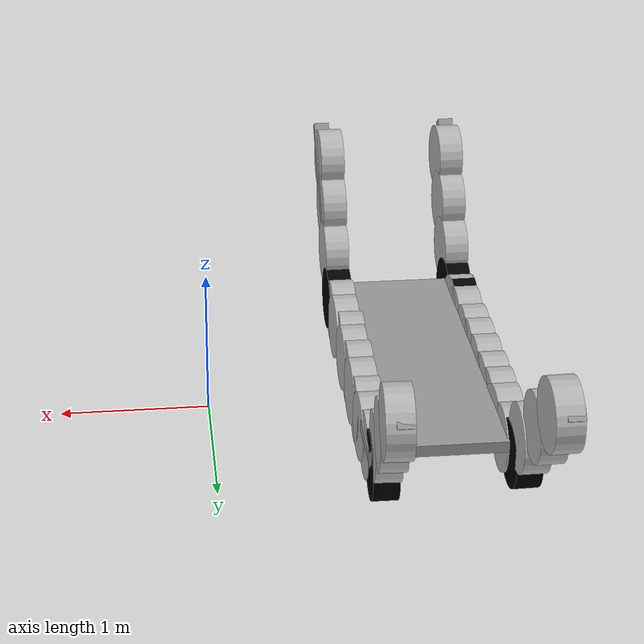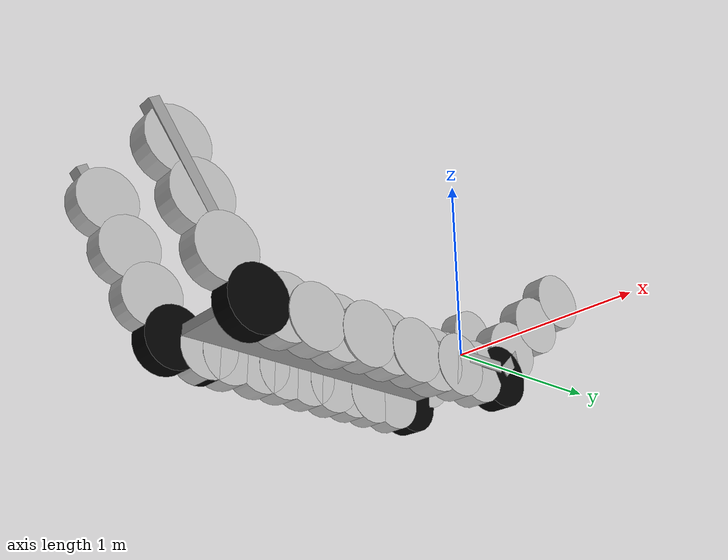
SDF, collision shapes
<?xml version='1.0'?>
<sdf version='1.7'>
  <model name='MoT24U'>
    <link name='link'>
      <pose>-0.963911 0.348344 0.430063 6e-06 1.5707 6e-06</pose>
      <inertial>
        <mass>0.0238016</mass>
        <inertia>
          <ixx>0.00033125</ixx>
          <ixy>0</ixy>
          <ixz>0</ixz>
          <iyy>0.00033125</iyy>
          <iyz>0</iyz>
          <izz>0.00055947</izz>
        </inertia>
        <pose>0 0 0 0 -0 0</pose>
      </inertial>
      <self_collide>0</self_collide>
      <enable_wind>0</enable_wind>
      <kinematic>0</kinematic>
      <gravity>1</gravity>
      <visual name='visual'>
        <pose>0 0 -0.08058 0 -0 0</pose>
        <geometry>
          <mesh>
            <uri>model://car_wheel/meshes/car_wheel.dae</uri>
          </mesh>
        </geometry>
        <material>
          <shader type='pixel'>
            <normal_map>__default__</normal_map>
          </shader>
          <emissive>0 0 0 1</emissive>
        </material>
        <transparency>0</transparency>
        <cast_shadows>1</cast_shadows>
      </visual>
      <collision name='collision'>
        <laser_retro>0</laser_retro>
        <max_contacts>10</max_contacts>
        <pose>0 0 0 0 -0 0</pose>
        <geometry>
          <cylinder>
            <radius>0.21682</radius>
            <length>0.16116</length>
          </cylinder>
        </geometry>
        <surface>
          <friction>
            <ode>
              <mu>1</mu>
              <mu2>1</mu2>
              <fdir1>0 0 1</fdir1>
              <slip1>0</slip1>
              <slip2>0</slip2>
            </ode>
            <torsional>
              <coefficient>1</coefficient>
              <patch_radius>0</patch_radius>
              <surface_radius>0</surface_radius>
              <use_patch_radius>1</use_patch_radius>
              <ode>
                <slip>0</slip>
              </ode>
            </torsional>
          </friction>
          <bounce>
            <restitution_coefficient>0</restitution_coefficient>
            <threshold>1e+06</threshold>
          </bounce>
          <contact>
            <collide_without_contact>0</collide_without_contact>
            <collide_without_contact_bitmask>1</collide_without_contact_bitmask>
            <collide_bitmask>1</collide_bitmask>
            <ode>
              <soft_cfm>0</soft_cfm>
              <soft_erp>0.2</soft_erp>
              <kp>1e+08</kp>
              <kd>1</kd>
              <max_vel>0.01</max_vel>
              <min_depth>0.005</min_depth>
            </ode>
            <bullet>
              <split_impulse>1</split_impulse>
              <split_impulse_penetration_threshold>-0.01</split_impulse_penetration_threshold>
              <soft_cfm>0</soft_cfm>
              <soft_erp>0.2</soft_erp>
              <kp>1e+08</kp>
              <kd>1</kd>
            </bullet>
          </contact>
        </surface>
      </collision>
    </link>
    <link name='link_1'>
      <inertial>
        <mass>0.159561</mass>
        <inertia>
          <ixx>0.0563091</ixx>
          <ixy>0</ixy>
          <ixz>0</ixz>
          <iyy>0.0133768</iyy>
          <iyz>0</iyz>
          <izz>0.0695258</izz>
        </inertia>
        <pose>0 0 0 0 -0 0</pose>
      </inertial>
      <pose>-1.38023 0.346647 0.500456 0 -9.2e-05 0</pose>
      <self_collide>0</self_collide>
      <enable_wind>0</enable_wind>
      <kinematic>0</kinematic>
      <visual name='visual'>
        <pose>0 0 0 0 -0 0</pose>
        <geometry>
          <box>
            <size>1 2.0564 0.077579</size>
          </box>
        </geometry>
        <material>
          <lighting>1</lighting>
          <script>
            <uri>file://media/materials/scripts/gazebo.material</uri>
            <name>Gazebo/Grey</name>
          </script>
          <shader type='pixel'/>
          <emissive>0 0 0 1</emissive>
        </material>
        <transparency>0</transparency>
        <cast_shadows>1</cast_shadows>
      </visual>
      <collision name='collision'>
        <laser_retro>0</laser_retro>
        <max_contacts>10</max_contacts>
        <pose>0 0 0 0 -0 0</pose>
        <geometry>
          <box>
            <size>1 2.0564 0.077579</size>
          </box>
        </geometry>
        <surface>
          <friction>
            <ode>
              <mu>1</mu>
              <mu2>1</mu2>
              <fdir1>0 0 0</fdir1>
              <slip1>0</slip1>
              <slip2>0</slip2>
            </ode>
            <torsional>
              <coefficient>1</coefficient>
              <patch_radius>0</patch_radius>
              <surface_radius>0</surface_radius>
              <use_patch_radius>1</use_patch_radius>
              <ode>
                <slip>0</slip>
              </ode>
            </torsional>
          </friction>
          <bounce>
            <restitution_coefficient>0</restitution_coefficient>
            <threshold>1e+06</threshold>
          </bounce>
          <contact>
            <collide_without_contact>0</collide_without_contact>
            <collide_without_contact_bitmask>1</collide_without_contact_bitmask>
            <collide_bitmask>1</collide_bitmask>
            <ode>
              <soft_cfm>0</soft_cfm>
              <soft_erp>0.2</soft_erp>
              <kp>1e+13</kp>
              <kd>1</kd>
              <max_vel>0.01</max_vel>
              <min_depth>0</min_depth>
            </ode>
            <bullet>
              <split_impulse>1</split_impulse>
              <split_impulse_penetration_threshold>-0.01</split_impulse_penetration_threshold>
              <soft_cfm>0</soft_cfm>
              <soft_erp>0.2</soft_erp>
              <kp>1e+13</kp>
              <kd>1</kd>
            </bullet>
          </contact>
        </surface>
      </collision>
    </link>
    <link name='link_1_clone'>
      <inertial>
        <mass>0.00937873</mass>
        <inertia>
          <ixx>0.00110956</ixx>
          <ixy>0</ixy>
          <ixz>0</ixz>
          <iyy>1.27818e-05</iyy>
          <iyz>0</iyz>
          <izz>0.00111294</izz>
        </inertia>
        <pose>0 0 0 0 -0 0</pose>
      </inertial>
      <pose>-0.933971 1.83039 0.8913 0.781604 -0.00013 0.006287</pose>
      <self_collide>0</self_collide>
      <enable_wind>0</enable_wind>
      <kinematic>0</kinematic>
      <visual name='visual'>
        <pose>0 0 0 0 -0 0</pose>
        <geometry>
          <box>
            <size>0.101664 1.18897 0.077579</size>
          </box>
        </geometry>
        <material>
          <lighting>1</lighting>
          <script>
            <uri>file://media/materials/scripts/gazebo.material</uri>
            <name>Gazebo/Grey</name>
          </script>
          <shader type='pixel'/>
          <emissive>0 0 0 1</emissive>
        </material>
        <transparency>0</transparency>
        <cast_shadows>1</cast_shadows>
      </visual>
      <collision name='collision'>
        <laser_retro>0</laser_retro>
        <max_contacts>10</max_contacts>
        <pose>0 0 0 0 -0 0</pose>
        <geometry>
          <box>
            <size>0.101664 1.18897 0.077579</size>
          </box>
        </geometry>
        <surface>
          <friction>
            <ode>
              <mu>1</mu>
              <mu2>1</mu2>
              <fdir1>0 0 0</fdir1>
              <slip1>0</slip1>
              <slip2>0</slip2>
            </ode>
            <torsional>
              <coefficient>1</coefficient>
              <patch_radius>0</patch_radius>
              <surface_radius>0</surface_radius>
              <use_patch_radius>1</use_patch_radius>
              <ode>
                <slip>0</slip>
              </ode>
            </torsional>
          </friction>
          <bounce>
            <restitution_coefficient>0</restitution_coefficient>
            <threshold>1e+06</threshold>
          </bounce>
          <contact>
            <collide_without_contact>0</collide_without_contact>
            <collide_without_contact_bitmask>1</collide_without_contact_bitmask>
            <collide_bitmask>1</collide_bitmask>
            <ode>
              <soft_cfm>0</soft_cfm>
              <soft_erp>0.2</soft_erp>
              <kp>1e+13</kp>
              <kd>1</kd>
              <max_vel>0.01</max_vel>
              <min_depth>0</min_depth>
            </ode>
            <bullet>
              <split_impulse>1</split_impulse>
              <split_impulse_penetration_threshold>-0.01</split_impulse_penetration_threshold>
              <soft_cfm>0</soft_cfm>
              <soft_erp>0.2</soft_erp>
              <kp>1e+13</kp>
              <kd>1</kd>
            </bullet>
          </contact>
        </surface>
      </collision>
    </link>
    <link name='link_1_clone_clone'>
      <inertial>
        <mass>0.00937873</mass>
        <inertia>
          <ixx>0.00110956</ixx>
          <ixy>0</ixy>
          <ixz>0</ixz>
          <iyy>1.27818e-05</iyy>
          <iyz>0</iyz>
          <izz>0.00111294</izz>
        </inertia>
        <pose>0 0 0 0 -0 0</pose>
      </inertial>
      <pose>-1.84231 1.82807 0.888138 0.77371 -0.000119 0.012574</pose>
      <self_collide>0</self_collide>
      <enable_wind>0</enable_wind>
      <kinematic>0</kinematic>
      <visual name='visual'>
        <pose>0 0 0 0 -0 0</pose>
        <geometry>
          <box>
            <size>0.101664 1.18897 0.077579</size>
          </box>
        </geometry>
        <material>
          <lighting>1</lighting>
          <script>
            <uri>file://media/materials/scripts/gazebo.material</uri>
            <name>Gazebo/Grey</name>
          </script>
          <shader type='pixel'/>
          <emissive>0 0 0 1</emissive>
        </material>
        <transparency>0</transparency>
        <cast_shadows>1</cast_shadows>
      </visual>
      <collision name='collision'>
        <laser_retro>0</laser_retro>
        <max_contacts>10</max_contacts>
        <pose>0 0 0 0 -0 0</pose>
        <geometry>
          <box>
            <size>0.101664 1.18897 0.077579</size>
          </box>
        </geometry>
        <surface>
          <friction>
            <ode>
              <mu>1</mu>
              <mu2>1</mu2>
              <fdir1>0 0 0</fdir1>
              <slip1>0</slip1>
              <slip2>0</slip2>
            </ode>
            <torsional>
              <coefficient>1</coefficient>
              <patch_radius>0</patch_radius>
              <surface_radius>0</surface_radius>
              <use_patch_radius>1</use_patch_radius>
              <ode>
                <slip>0</slip>
              </ode>
            </torsional>
          </friction>
          <bounce>
            <restitution_coefficient>0</restitution_coefficient>
            <threshold>1e+06</threshold>
          </bounce>
          <contact>
            <collide_without_contact>0</collide_without_contact>
            <collide_without_contact_bitmask>1</collide_without_contact_bitmask>
            <collide_bitmask>1</collide_bitmask>
            <ode>
              <soft_cfm>0</soft_cfm>
              <soft_erp>0.2</soft_erp>
              <kp>1e+13</kp>
              <kd>1</kd>
              <max_vel>0.01</max_vel>
              <min_depth>0</min_depth>
            </ode>
            <bullet>
              <split_impulse>1</split_impulse>
              <split_impulse_penetration_threshold>-0.01</split_impulse_penetration_threshold>
              <soft_cfm>0</soft_cfm>
              <soft_erp>0.2</soft_erp>
              <kp>1e+13</kp>
              <kd>1</kd>
            </bullet>
          </contact>
        </surface>
      </collision>
    </link>
    <link name='link_1_clone_clone_0_clone'>
      <inertial>
        <mass>0.00937873</mass>
        <inertia>
          <ixx>0.00110956</ixx>
          <ixy>0</ixy>
          <ixz>0</ixz>
          <iyy>1.27818e-05</iyy>
          <iyz>0</iyz>
          <izz>0.00111294</izz>
        </inertia>
        <pose>0 0 0 0 -0 0</pose>
      </inertial>
      <pose>-1.82187 -1.08731 0.953279 2.2377 -5.8e-05 0.01886</pose>
      <self_collide>0</self_collide>
      <enable_wind>0</enable_wind>
      <kinematic>0</kinematic>
      <visual name='visual'>
        <pose>0 0 0 0 -0 0</pose>
        <geometry>
          <box>
            <size>0.101664 1.18897 0.077579</size>
          </box>
        </geometry>
        <material>
          <lighting>1</lighting>
          <script>
            <uri>file://media/materials/scripts/gazebo.material</uri>
            <name>Gazebo/Grey</name>
          </script>
          <shader type='pixel'/>
          <emissive>0 0 0 1</emissive>
        </material>
        <transparency>0</transparency>
        <cast_shadows>1</cast_shadows>
      </visual>
      <collision name='collision'>
        <laser_retro>0</laser_retro>
        <max_contacts>10</max_contacts>
        <pose>0 0 0 0 -0 0</pose>
        <geometry>
          <box>
            <size>0.101664 1.18897 0.077579</size>
          </box>
        </geometry>
        <surface>
          <friction>
            <ode>
              <mu>1</mu>
              <mu2>1</mu2>
              <fdir1>0 0 0</fdir1>
              <slip1>0</slip1>
              <slip2>0</slip2>
            </ode>
            <torsional>
              <coefficient>1</coefficient>
              <patch_radius>0</patch_radius>
              <surface_radius>0</surface_radius>
              <use_patch_radius>1</use_patch_radius>
              <ode>
                <slip>0</slip>
              </ode>
            </torsional>
          </friction>
          <bounce>
            <restitution_coefficient>0</restitution_coefficient>
            <threshold>1e+06</threshold>
          </bounce>
          <contact>
            <collide_without_contact>0</collide_without_contact>
            <collide_without_contact_bitmask>1</collide_without_contact_bitmask>
            <collide_bitmask>1</collide_bitmask>
            <ode>
              <soft_cfm>0</soft_cfm>
              <soft_erp>0.2</soft_erp>
              <kp>1e+13</kp>
              <kd>1</kd>
              <max_vel>0.01</max_vel>
              <min_depth>0</min_depth>
            </ode>
            <bullet>
              <split_impulse>1</split_impulse>
              <split_impulse_penetration_threshold>-0.01</split_impulse_penetration_threshold>
              <soft_cfm>0</soft_cfm>
              <soft_erp>0.2</soft_erp>
              <kp>1e+13</kp>
              <kd>1</kd>
            </bullet>
          </contact>
        </surface>
      </collision>
    </link>
    <link name='link_1_clone_clone_0_clone_clone'>
      <inertial>
        <mass>0.00937873</mass>
        <inertia>
          <ixx>0.00110956</ixx>
          <ixy>0</ixy>
          <ixz>0</ixz>
          <iyy>1.27818e-05</iyy>
          <iyz>0</iyz>
          <izz>0.00111294</izz>
        </inertia>
        <pose>0 0 0 0 -0 0</pose>
      </inertial>
      <pose>-0.923124 -1.07843 0.955956 2.22981 5.3e-05 0.025146</pose>
      <self_collide>0</self_collide>
      <enable_wind>0</enable_wind>
      <kinematic>0</kinematic>
      <visual name='visual'>
        <pose>0 0 0 0 -0 0</pose>
        <geometry>
          <box>
            <size>0.101664 1.18897 0.077579</size>
          </box>
        </geometry>
        <material>
          <lighting>1</lighting>
          <script>
            <uri>file://media/materials/scripts/gazebo.material</uri>
            <name>Gazebo/Grey</name>
          </script>
          <shader type='pixel'/>
          <emissive>0 0 0 1</emissive>
        </material>
        <transparency>0</transparency>
        <cast_shadows>1</cast_shadows>
      </visual>
      <collision name='collision'>
        <laser_retro>0</laser_retro>
        <max_contacts>10</max_contacts>
        <pose>0 0 0 0 -0 0</pose>
        <geometry>
          <box>
            <size>0.101664 1.18897 0.077579</size>
          </box>
        </geometry>
        <surface>
          <friction>
            <ode>
              <mu>1</mu>
              <mu2>1</mu2>
              <fdir1>0 0 0</fdir1>
              <slip1>0</slip1>
              <slip2>0</slip2>
            </ode>
            <torsional>
              <coefficient>1</coefficient>
              <patch_radius>0</patch_radius>
              <surface_radius>0</surface_radius>
              <use_patch_radius>1</use_patch_radius>
              <ode>
                <slip>0</slip>
              </ode>
            </torsional>
          </friction>
          <bounce>
            <restitution_coefficient>0</restitution_coefficient>
            <threshold>1e+06</threshold>
          </bounce>
          <contact>
            <collide_without_contact>0</collide_without_contact>
            <collide_without_contact_bitmask>1</collide_without_contact_bitmask>
            <collide_bitmask>1</collide_bitmask>
            <ode>
              <soft_cfm>0</soft_cfm>
              <soft_erp>0.2</soft_erp>
              <kp>1e+13</kp>
              <kd>1</kd>
              <max_vel>0.01</max_vel>
              <min_depth>0</min_depth>
            </ode>
            <bullet>
              <split_impulse>1</split_impulse>
              <split_impulse_penetration_threshold>-0.01</split_impulse_penetration_threshold>
              <soft_cfm>0</soft_cfm>
              <soft_erp>0.2</soft_erp>
              <kp>1e+13</kp>
              <kd>1</kd>
            </bullet>
          </contact>
        </surface>
      </collision>
    </link>
    <link name='link_clone'>
      <pose>-1.80469 0.343058 0.430025 5.4e-05 1.57061 5.4e-05</pose>
      <inertial>
        <mass>0.0238016</mass>
        <inertia>
          <ixx>0.00033125</ixx>
          <ixy>0</ixy>
          <ixz>0</ixz>
          <iyy>0.00033125</iyy>
          <iyz>0</iyz>
          <izz>0.00055947</izz>
        </inertia>
        <pose>0 0 0 0 -0 0</pose>
      </inertial>
      <self_collide>0</self_collide>
      <enable_wind>0</enable_wind>
      <kinematic>0</kinematic>
      <gravity>1</gravity>
      <visual name='visual'>
        <pose>0 0 -0.08058 0 -0 0</pose>
        <geometry>
          <mesh>
            <uri>model://car_wheel/meshes/car_wheel.dae</uri>
          </mesh>
        </geometry>
        <material>
          <shader type='pixel'>
            <normal_map>__default__</normal_map>
          </shader>
          <emissive>0 0 0 1</emissive>
        </material>
        <transparency>0</transparency>
        <cast_shadows>1</cast_shadows>
      </visual>
      <collision name='collision'>
        <laser_retro>0</laser_retro>
        <max_contacts>10</max_contacts>
        <pose>0 0 0 0 -0 0</pose>
        <geometry>
          <cylinder>
            <radius>0.21682</radius>
            <length>0.16116</length>
          </cylinder>
        </geometry>
        <surface>
          <friction>
            <ode>
              <mu>1</mu>
              <mu2>1</mu2>
              <fdir1>0 0 0</fdir1>
              <slip1>0</slip1>
              <slip2>0</slip2>
            </ode>
            <torsional>
              <coefficient>1</coefficient>
              <patch_radius>0</patch_radius>
              <surface_radius>0</surface_radius>
              <use_patch_radius>1</use_patch_radius>
              <ode>
                <slip>0</slip>
              </ode>
            </torsional>
          </friction>
          <bounce>
            <restitution_coefficient>0</restitution_coefficient>
            <threshold>1e+06</threshold>
          </bounce>
          <contact>
            <collide_without_contact>0</collide_without_contact>
            <collide_without_contact_bitmask>1</collide_without_contact_bitmask>
            <collide_bitmask>1</collide_bitmask>
            <ode>
              <soft_cfm>0</soft_cfm>
              <soft_erp>0.2</soft_erp>
              <kp>1e+13</kp>
              <kd>1</kd>
              <max_vel>0.01</max_vel>
              <min_depth>0</min_depth>
            </ode>
            <bullet>
              <split_impulse>1</split_impulse>
              <split_impulse_penetration_threshold>-0.01</split_impulse_penetration_threshold>
              <soft_cfm>0</soft_cfm>
              <soft_erp>0.2</soft_erp>
              <kp>1e+13</kp>
              <kd>1</kd>
            </bullet>
          </contact>
        </surface>
      </collision>
    </link>
    <link name='link_clone_0'>
      <pose>-0.958826 -0.464567 0.436472 5.4e-05 1.57061 5.4e-05</pose>
      <inertial>
        <mass>0.0238016</mass>
        <inertia>
          <ixx>0.00033125</ixx>
          <ixy>0</ixy>
          <ixz>0</ixz>
          <iyy>0.00033125</iyy>
          <iyz>0</iyz>
          <izz>0.00055947</izz>
        </inertia>
        <pose>0 0 0 0 -0 0</pose>
      </inertial>
      <self_collide>0</self_collide>
      <enable_wind>0</enable_wind>
      <kinematic>0</kinematic>
      <gravity>1</gravity>
      <visual name='visual'>
        <pose>0 0 -0.08058 0 -0 0</pose>
        <geometry>
          <mesh>
            <uri>model://car_wheel/meshes/car_wheel.dae</uri>
          </mesh>
        </geometry>
        <material>
          <shader type='pixel'>
            <normal_map>__default__</normal_map>
          </shader>
          <emissive>0 0 0 1</emissive>
        </material>
        <transparency>0</transparency>
        <cast_shadows>1</cast_shadows>
      </visual>
      <collision name='collision'>
        <laser_retro>0</laser_retro>
        <max_contacts>10</max_contacts>
        <pose>0 0 0 0 -0 0</pose>
        <geometry>
          <cylinder>
            <radius>0.21682</radius>
            <length>0.16116</length>
          </cylinder>
        </geometry>
        <surface>
          <friction>
            <ode>
              <mu>1</mu>
              <mu2>1</mu2>
              <fdir1>0 0 0</fdir1>
              <slip1>0</slip1>
              <slip2>0</slip2>
            </ode>
            <torsional>
              <coefficient>1</coefficient>
              <patch_radius>0</patch_radius>
              <surface_radius>0</surface_radius>
              <use_patch_radius>1</use_patch_radius>
              <ode>
                <slip>0</slip>
              </ode>
            </torsional>
          </friction>
          <bounce>
            <restitution_coefficient>0</restitution_coefficient>
            <threshold>1e+06</threshold>
          </bounce>
          <contact>
            <collide_without_contact>0</collide_without_contact>
            <collide_without_contact_bitmask>1</collide_without_contact_bitmask>
            <collide_bitmask>1</collide_bitmask>
            <ode>
              <soft_cfm>0</soft_cfm>
              <soft_erp>0.2</soft_erp>
              <kp>1e+13</kp>
              <kd>1</kd>
              <max_vel>0.01</max_vel>
              <min_depth>0</min_depth>
            </ode>
            <bullet>
              <split_impulse>1</split_impulse>
              <split_impulse_penetration_threshold>-0.01</split_impulse_penetration_threshold>
              <soft_cfm>0</soft_cfm>
              <soft_erp>0.2</soft_erp>
              <kp>1e+13</kp>
              <kd>1</kd>
            </bullet>
          </contact>
        </surface>
      </collision>
    </link>
    <link name='link_clone_1'>
      <pose>-1.79958 -0.469845 0.436437 5.4e-05 1.57061 5.4e-05</pose>
      <inertial>
        <mass>0.0238016</mass>
        <inertia>
          <ixx>0.00033125</ixx>
          <ixy>0</ixy>
          <ixz>0</ixz>
          <iyy>0.00033125</iyy>
          <iyz>0</iyz>
          <izz>0.00055947</izz>
        </inertia>
        <pose>0 0 0 0 -0 0</pose>
      </inertial>
      <self_collide>0</self_collide>
      <enable_wind>0</enable_wind>
      <kinematic>0</kinematic>
      <gravity>1</gravity>
      <visual name='visual'>
        <pose>0 0 -0.08058 0 -0 0</pose>
        <geometry>
          <mesh>
            <uri>model://car_wheel/meshes/car_wheel.dae</uri>
          </mesh>
        </geometry>
        <material>
          <shader type='pixel'>
            <normal_map>__default__</normal_map>
          </shader>
          <emissive>0 0 0 1</emissive>
        </material>
        <transparency>0</transparency>
        <cast_shadows>1</cast_shadows>
      </visual>
      <collision name='collision'>
        <laser_retro>0</laser_retro>
        <max_contacts>10</max_contacts>
        <pose>0 0 0 0 -0 0</pose>
        <geometry>
          <cylinder>
            <radius>0.21682</radius>
            <length>0.16116</length>
          </cylinder>
        </geometry>
        <surface>
          <friction>
            <ode>
              <mu>1</mu>
              <mu2>1</mu2>
              <fdir1>0 0 0</fdir1>
              <slip1>0</slip1>
              <slip2>0</slip2>
            </ode>
            <torsional>
              <coefficient>1</coefficient>
              <patch_radius>0</patch_radius>
              <surface_radius>0</surface_radius>
              <use_patch_radius>1</use_patch_radius>
              <ode>
                <slip>0</slip>
              </ode>
            </torsional>
          </friction>
          <bounce>
            <restitution_coefficient>0</restitution_coefficient>
            <threshold>1e+06</threshold>
          </bounce>
          <contact>
            <collide_without_contact>0</collide_without_contact>
            <collide_without_contact_bitmask>1</collide_without_contact_bitmask>
            <collide_bitmask>1</collide_bitmask>
            <ode>
              <soft_cfm>0</soft_cfm>
              <soft_erp>0.2</soft_erp>
              <kp>1e+13</kp>
              <kd>1</kd>
              <max_vel>0.01</max_vel>
              <min_depth>0</min_depth>
            </ode>
            <bullet>
              <split_impulse>1</split_impulse>
              <split_impulse_penetration_threshold>-0.01</split_impulse_penetration_threshold>
              <soft_cfm>0</soft_cfm>
              <soft_erp>0.2</soft_erp>
              <kp>1e+13</kp>
              <kd>1</kd>
            </bullet>
          </contact>
        </surface>
      </collision>
    </link>
    <link name='link_clone_1_clone'>
      <pose>-0.95565 -1.25875 1.23165 -1.54215 1.5629 -1.53588</pose>
      <inertial>
        <mass>0.0238016</mass>
        <inertia>
          <ixx>0.00033125</ixx>
          <ixy>0</ixy>
          <ixz>0</ixz>
          <iyy>0.00033125</iyy>
          <iyz>0</iyz>
          <izz>0.00055947</izz>
        </inertia>
        <pose>0 0 0 0 -0 0</pose>
      </inertial>
      <self_collide>0</self_collide>
      <enable_wind>0</enable_wind>
      <kinematic>0</kinematic>
      <gravity>1</gravity>
      <visual name='visual'>
        <pose>0 0 -0.08058 0 -0 0</pose>
        <geometry>
          <mesh>
            <uri>model://car_wheel/meshes/car_wheel.dae</uri>
          </mesh>
        </geometry>
        <material>
          <shader type='pixel'>
            <normal_map>__default__</normal_map>
          </shader>
          <emissive>0 0 0 1</emissive>
        </material>
        <transparency>0</transparency>
        <cast_shadows>1</cast_shadows>
      </visual>
      <collision name='collision'>
        <laser_retro>0</laser_retro>
        <max_contacts>10</max_contacts>
        <pose>0 0 0 0 -0 0</pose>
        <geometry>
          <cylinder>
            <radius>0.21682</radius>
            <length>0.16116</length>
          </cylinder>
        </geometry>
        <surface>
          <friction>
            <ode>
              <mu>1</mu>
              <mu2>1</mu2>
              <fdir1>0 0 0</fdir1>
              <slip1>0</slip1>
              <slip2>0</slip2>
            </ode>
            <torsional>
              <coefficient>1</coefficient>
              <patch_radius>0</patch_radius>
              <surface_radius>0</surface_radius>
              <use_patch_radius>1</use_patch_radius>
              <ode>
                <slip>0</slip>
              </ode>
            </torsional>
          </friction>
          <bounce>
            <restitution_coefficient>0</restitution_coefficient>
            <threshold>1e+06</threshold>
          </bounce>
          <contact>
            <collide_without_contact>0</collide_without_contact>
            <collide_without_contact_bitmask>1</collide_without_contact_bitmask>
            <collide_bitmask>1</collide_bitmask>
            <ode>
              <soft_cfm>0</soft_cfm>
              <soft_erp>0.2</soft_erp>
              <kp>1e+13</kp>
              <kd>1</kd>
              <max_vel>0.01</max_vel>
              <min_depth>0</min_depth>
            </ode>
            <bullet>
              <split_impulse>1</split_impulse>
              <split_impulse_penetration_threshold>-0.01</split_impulse_penetration_threshold>
              <soft_cfm>0</soft_cfm>
              <soft_erp>0.2</soft_erp>
              <kp>1e+13</kp>
              <kd>1</kd>
            </bullet>
          </contact>
        </surface>
      </collision>
    </link>
    <link name='link_clone_1_clone_0'>
      <pose>-1.79934 -0.903843 0.680233 -1.54215 1.5629 -1.53588</pose>
      <inertial>
        <mass>0.0238016</mass>
        <inertia>
          <ixx>0.00033125</ixx>
          <ixy>0</ixy>
          <ixz>0</ixz>
          <iyy>0.00033125</iyy>
          <iyz>0</iyz>
          <izz>0.00055947</izz>
        </inertia>
        <pose>0 0 0 0 -0 0</pose>
      </inertial>
      <self_collide>0</self_collide>
      <enable_wind>0</enable_wind>
      <kinematic>0</kinematic>
      <gravity>1</gravity>
      <visual name='visual'>
        <pose>0 0 -0.08058 0 -0 0</pose>
        <geometry>
          <mesh>
            <uri>model://car_wheel/meshes/car_wheel.dae</uri>
          </mesh>
        </geometry>
        <material>
          <shader type='pixel'>
            <normal_map>__default__</normal_map>
          </shader>
          <emissive>0 0 0 1</emissive>
        </material>
        <transparency>0</transparency>
        <cast_shadows>1</cast_shadows>
      </visual>
      <collision name='collision'>
        <laser_retro>0</laser_retro>
        <max_contacts>10</max_contacts>
        <pose>0 0 0 0 -0 0</pose>
        <geometry>
          <cylinder>
            <radius>0.21682</radius>
            <length>0.16116</length>
          </cylinder>
        </geometry>
        <surface>
          <friction>
            <ode>
              <mu>1</mu>
              <mu2>1</mu2>
              <fdir1>0 0 0</fdir1>
              <slip1>0</slip1>
              <slip2>0</slip2>
            </ode>
            <torsional>
              <coefficient>1</coefficient>
              <patch_radius>0</patch_radius>
              <surface_radius>0</surface_radius>
              <use_patch_radius>1</use_patch_radius>
              <ode>
                <slip>0</slip>
              </ode>
            </torsional>
          </friction>
          <bounce>
            <restitution_coefficient>0</restitution_coefficient>
            <threshold>1e+06</threshold>
          </bounce>
          <contact>
            <collide_without_contact>0</collide_without_contact>
            <collide_without_contact_bitmask>1</collide_without_contact_bitmask>
            <collide_bitmask>1</collide_bitmask>
            <ode>
              <soft_cfm>0</soft_cfm>
              <soft_erp>0.2</soft_erp>
              <kp>1e+13</kp>
              <kd>1</kd>
              <max_vel>0.01</max_vel>
              <min_depth>0</min_depth>
            </ode>
            <bullet>
              <split_impulse>1</split_impulse>
              <split_impulse_penetration_threshold>-0.01</split_impulse_penetration_threshold>
              <soft_cfm>0</soft_cfm>
              <soft_erp>0.2</soft_erp>
              <kp>1e+13</kp>
              <kd>1</kd>
            </bullet>
          </contact>
        </surface>
      </collision>
    </link>
    <link name='link_clone_1_clone_1'>
      <pose>-1.79978 -1.2705 1.22634 -1.54215 1.5629 -1.53588</pose>
      <inertial>
        <mass>0.0238016</mass>
        <inertia>
          <ixx>0.00033125</ixx>
          <ixy>0</ixy>
          <ixz>0</ixz>
          <iyy>0.00033125</iyy>
          <iyz>0</iyz>
          <izz>0.00055947</izz>
        </inertia>
        <pose>0 0 0 0 -0 0</pose>
      </inertial>
      <self_collide>0</self_collide>
      <enable_wind>0</enable_wind>
      <kinematic>0</kinematic>
      <gravity>1</gravity>
      <visual name='visual'>
        <pose>0 0 -0.08058 0 -0 0</pose>
        <geometry>
          <mesh>
            <uri>model://car_wheel/meshes/car_wheel.dae</uri>
          </mesh>
        </geometry>
        <material>
          <shader type='pixel'>
            <normal_map>__default__</normal_map>
          </shader>
          <emissive>0 0 0 1</emissive>
        </material>
        <transparency>0</transparency>
        <cast_shadows>1</cast_shadows>
      </visual>
      <collision name='collision'>
        <laser_retro>0</laser_retro>
        <max_contacts>10</max_contacts>
        <pose>0 0 0 0 -0 0</pose>
        <geometry>
          <cylinder>
            <radius>0.21682</radius>
            <length>0.16116</length>
          </cylinder>
        </geometry>
        <surface>
          <friction>
            <ode>
              <mu>1</mu>
              <mu2>1</mu2>
              <fdir1>0 0 0</fdir1>
              <slip1>0</slip1>
              <slip2>0</slip2>
            </ode>
            <torsional>
              <coefficient>1</coefficient>
              <patch_radius>0</patch_radius>
              <surface_radius>0</surface_radius>
              <use_patch_radius>1</use_patch_radius>
              <ode>
                <slip>0</slip>
              </ode>
            </torsional>
          </friction>
          <bounce>
            <restitution_coefficient>0</restitution_coefficient>
            <threshold>1e+06</threshold>
          </bounce>
          <contact>
            <collide_without_contact>0</collide_without_contact>
            <collide_without_contact_bitmask>1</collide_without_contact_bitmask>
            <collide_bitmask>1</collide_bitmask>
            <ode>
              <soft_cfm>0</soft_cfm>
              <soft_erp>0.2</soft_erp>
              <kp>1e+13</kp>
              <kd>1</kd>
              <max_vel>0.01</max_vel>
              <min_depth>0</min_depth>
            </ode>
            <bullet>
              <split_impulse>1</split_impulse>
              <split_impulse_penetration_threshold>-0.01</split_impulse_penetration_threshold>
              <soft_cfm>0</soft_cfm>
              <soft_erp>0.2</soft_erp>
              <kp>1e+13</kp>
              <kd>1</kd>
            </bullet>
          </contact>
        </surface>
      </collision>
    </link>
    <link name='link_clone_1_clone_2'>
      <pose>-1.7992 -1.08717 0.953291 -1.54215 1.5629 -1.53588</pose>
      <inertial>
        <mass>0.0238016</mass>
        <inertia>
          <ixx>0.00033125</ixx>
          <ixy>0</ixy>
          <ixz>0</ixz>
          <iyy>0.00033125</iyy>
          <iyz>0</iyz>
          <izz>0.00055947</izz>
        </inertia>
        <pose>0 0 0 0 -0 0</pose>
      </inertial>
      <self_collide>0</self_collide>
      <enable_wind>0</enable_wind>
      <kinematic>0</kinematic>
      <gravity>1</gravity>
      <visual name='visual'>
        <pose>0 0 -0.08058 0 -0 0</pose>
        <geometry>
          <mesh>
            <uri>model://car_wheel/meshes/car_wheel.dae</uri>
          </mesh>
        </geometry>
        <material>
          <shader type='pixel'>
            <normal_map>__default__</normal_map>
          </shader>
          <emissive>0 0 0 1</emissive>
        </material>
        <transparency>0</transparency>
        <cast_shadows>1</cast_shadows>
      </visual>
      <collision name='collision'>
        <laser_retro>0</laser_retro>
        <max_contacts>10</max_contacts>
        <pose>0 0 0 0 -0 0</pose>
        <geometry>
          <cylinder>
            <radius>0.21682</radius>
            <length>0.16116</length>
          </cylinder>
        </geometry>
        <surface>
          <friction>
            <ode>
              <mu>1</mu>
              <mu2>1</mu2>
              <fdir1>0 0 0</fdir1>
              <slip1>0</slip1>
              <slip2>0</slip2>
            </ode>
            <torsional>
              <coefficient>1</coefficient>
              <patch_radius>0</patch_radius>
              <surface_radius>0</surface_radius>
              <use_patch_radius>1</use_patch_radius>
              <ode>
                <slip>0</slip>
              </ode>
            </torsional>
          </friction>
          <bounce>
            <restitution_coefficient>0</restitution_coefficient>
            <threshold>1e+06</threshold>
          </bounce>
          <contact>
            <collide_without_contact>0</collide_without_contact>
            <collide_without_contact_bitmask>1</collide_without_contact_bitmask>
            <collide_bitmask>1</collide_bitmask>
            <ode>
              <soft_cfm>0</soft_cfm>
              <soft_erp>0.2</soft_erp>
              <kp>1e+13</kp>
              <kd>1</kd>
              <max_vel>0.01</max_vel>
              <min_depth>0</min_depth>
            </ode>
            <bullet>
              <split_impulse>1</split_impulse>
              <split_impulse_penetration_threshold>-0.01</split_impulse_penetration_threshold>
              <soft_cfm>0</soft_cfm>
              <soft_erp>0.2</soft_erp>
              <kp>1e+13</kp>
              <kd>1</kd>
            </bullet>
          </contact>
        </surface>
      </collision>
    </link>
    <link name='link_clone_1_clone_3'>
      <pose>-0.953766 -0.898521 0.680245 -1.5422 1.5629 -1.53593</pose>
      <inertial>
        <mass>0.0238016</mass>
        <inertia>
          <ixx>0.00033125</ixx>
          <ixy>0</ixy>
          <ixz>0</ixz>
          <iyy>0.00033125</iyy>
          <iyz>0</iyz>
          <izz>0.00055947</izz>
        </inertia>
        <pose>0 0 0 0 -0 0</pose>
      </inertial>
      <self_collide>0</self_collide>
      <enable_wind>0</enable_wind>
      <kinematic>0</kinematic>
      <gravity>1</gravity>
      <visual name='visual'>
        <pose>0 0 -0.08058 0 -0 0</pose>
        <geometry>
          <mesh>
            <uri>model://car_wheel/meshes/car_wheel.dae</uri>
          </mesh>
        </geometry>
        <material>
          <shader type='pixel'>
            <normal_map>__default__</normal_map>
          </shader>
          <emissive>0 0 0 1</emissive>
        </material>
        <transparency>0</transparency>
        <cast_shadows>1</cast_shadows>
      </visual>
      <collision name='collision'>
        <laser_retro>0</laser_retro>
        <max_contacts>10</max_contacts>
        <pose>0 0 0 0 -0 0</pose>
        <geometry>
          <cylinder>
            <radius>0.21682</radius>
            <length>0.16116</length>
          </cylinder>
        </geometry>
        <surface>
          <friction>
            <ode>
              <mu>1</mu>
              <mu2>1</mu2>
              <fdir1>0 0 0</fdir1>
              <slip1>0</slip1>
              <slip2>0</slip2>
            </ode>
            <torsional>
              <coefficient>1</coefficient>
              <patch_radius>0</patch_radius>
              <surface_radius>0</surface_radius>
              <use_patch_radius>1</use_patch_radius>
              <ode>
                <slip>0</slip>
              </ode>
            </torsional>
          </friction>
          <bounce>
            <restitution_coefficient>0</restitution_coefficient>
            <threshold>1e+06</threshold>
          </bounce>
          <contact>
            <collide_without_contact>0</collide_without_contact>
            <collide_without_contact_bitmask>1</collide_without_contact_bitmask>
            <collide_bitmask>1</collide_bitmask>
            <ode>
              <soft_cfm>0</soft_cfm>
              <soft_erp>0.2</soft_erp>
              <kp>1e+13</kp>
              <kd>1</kd>
              <max_vel>0.01</max_vel>
              <min_depth>0</min_depth>
            </ode>
            <bullet>
              <split_impulse>1</split_impulse>
              <split_impulse_penetration_threshold>-0.01</split_impulse_penetration_threshold>
              <soft_cfm>0</soft_cfm>
              <soft_erp>0.2</soft_erp>
              <kp>1e+13</kp>
              <kd>1</kd>
            </bullet>
          </contact>
        </surface>
      </collision>
    </link>
    <link name='link_clone_1_clone_4'>
      <pose>-0.954958 -1.07864 0.955952 -1.54215 1.5629 -1.53588</pose>
      <inertial>
        <mass>0.0238016</mass>
        <inertia>
          <ixx>0.00033125</ixx>
          <ixy>0</ixy>
          <ixz>0</ixz>
          <iyy>0.00033125</iyy>
          <iyz>0</iyz>
          <izz>0.00055947</izz>
        </inertia>
        <pose>0 0 0 0 -0 0</pose>
      </inertial>
      <self_collide>0</self_collide>
      <enable_wind>0</enable_wind>
      <kinematic>0</kinematic>
      <gravity>1</gravity>
      <visual name='visual'>
        <pose>0 0 -0.08058 0 -0 0</pose>
        <geometry>
          <mesh>
            <uri>model://car_wheel/meshes/car_wheel.dae</uri>
          </mesh>
        </geometry>
        <material>
          <shader type='pixel'>
            <normal_map>__default__</normal_map>
          </shader>
          <emissive>0 0 0 1</emissive>
        </material>
        <transparency>0</transparency>
        <cast_shadows>1</cast_shadows>
      </visual>
      <collision name='collision'>
        <laser_retro>0</laser_retro>
        <max_contacts>10</max_contacts>
        <pose>0 0 0 0 -0 0</pose>
        <geometry>
          <cylinder>
            <radius>0.21682</radius>
            <length>0.16116</length>
          </cylinder>
        </geometry>
        <surface>
          <friction>
            <ode>
              <mu>1</mu>
              <mu2>1</mu2>
              <fdir1>0 0 0</fdir1>
              <slip1>0</slip1>
              <slip2>0</slip2>
            </ode>
            <torsional>
              <coefficient>1</coefficient>
              <patch_radius>0</patch_radius>
              <surface_radius>0</surface_radius>
              <use_patch_radius>1</use_patch_radius>
              <ode>
                <slip>0</slip>
              </ode>
            </torsional>
          </friction>
          <bounce>
            <restitution_coefficient>0</restitution_coefficient>
            <threshold>1e+06</threshold>
          </bounce>
          <contact>
            <collide_without_contact>0</collide_without_contact>
            <collide_without_contact_bitmask>1</collide_without_contact_bitmask>
            <collide_bitmask>1</collide_bitmask>
            <ode>
              <soft_cfm>0</soft_cfm>
              <soft_erp>0.2</soft_erp>
              <kp>1e+13</kp>
              <kd>1</kd>
              <max_vel>0.01</max_vel>
              <min_depth>0</min_depth>
            </ode>
            <bullet>
              <split_impulse>1</split_impulse>
              <split_impulse_penetration_threshold>-0.01</split_impulse_penetration_threshold>
              <soft_cfm>0</soft_cfm>
              <soft_erp>0.2</soft_erp>
              <kp>1e+13</kp>
              <kd>1</kd>
            </bullet>
          </contact>
        </surface>
      </collision>
    </link>
    <link name='link_clone_1_clone_5'>
      <pose>-0.955082 -0.671309 0.42999 -1.54232 1.5629 -1.53603</pose>
      <inertial>
        <mass>0.0238016</mass>
        <inertia>
          <ixx>0.00033125</ixx>
          <ixy>0</ixy>
          <ixz>0</ixz>
          <iyy>0.00033125</iyy>
          <iyz>0</iyz>
          <izz>0.00055947</izz>
        </inertia>
        <pose>0 0 0 0 -0 0</pose>
      </inertial>
      <self_collide>0</self_collide>
      <enable_wind>0</enable_wind>
      <kinematic>0</kinematic>
      <gravity>1</gravity>
      <visual name='visual'>
        <pose>0 0 -0.08058 0 -0 0</pose>
        <geometry>
          <mesh>
            <uri>model://car_wheel/meshes/car_wheel.dae</uri>
          </mesh>
        </geometry>
        <material>
          <shader type='pixel'>
            <normal_map>__default__</normal_map>
          </shader>
          <emissive>0 0 0 1</emissive>
          <script>
            <name>ModelPreview_7::link_clone_1_clone_5::visual_MATERIAL_</name>
            <uri>__default__</uri>
          </script>
          <ambient>0 0 0 1</ambient>
          <diffuse>0 0 0 1</diffuse>
          <specular>0 0 0 1</specular>
        </material>
        <transparency>0</transparency>
        <cast_shadows>1</cast_shadows>
      </visual>
      <collision name='collision'>
        <laser_retro>0</laser_retro>
        <max_contacts>10</max_contacts>
        <pose>0 0 0 0 -0 0</pose>
        <geometry>
          <cylinder>
            <radius>0.21682</radius>
            <length>0.16116</length>
          </cylinder>
        </geometry>
        <surface>
          <friction>
            <ode>
              <mu>1</mu>
              <mu2>1</mu2>
              <fdir1>0 0 0</fdir1>
              <slip1>0</slip1>
              <slip2>0</slip2>
            </ode>
            <torsional>
              <coefficient>1</coefficient>
              <patch_radius>0</patch_radius>
              <surface_radius>0</surface_radius>
              <use_patch_radius>1</use_patch_radius>
              <ode>
                <slip>0</slip>
              </ode>
            </torsional>
          </friction>
          <bounce>
            <restitution_coefficient>0</restitution_coefficient>
            <threshold>1e+06</threshold>
          </bounce>
          <contact>
            <collide_without_contact>0</collide_without_contact>
            <collide_without_contact_bitmask>1</collide_without_contact_bitmask>
            <collide_bitmask>1</collide_bitmask>
            <ode>
              <soft_cfm>0</soft_cfm>
              <soft_erp>0.2</soft_erp>
              <kp>1e+13</kp>
              <kd>1</kd>
              <max_vel>0.01</max_vel>
              <min_depth>0</min_depth>
            </ode>
            <bullet>
              <split_impulse>1</split_impulse>
              <split_impulse_penetration_threshold>-0.01</split_impulse_penetration_threshold>
              <soft_cfm>0</soft_cfm>
              <soft_erp>0.2</soft_erp>
              <kp>1e+13</kp>
              <kd>1</kd>
            </bullet>
          </contact>
        </surface>
      </collision>
    </link>
    <link name='link_clone_1_clone_5_clone'>
      <pose>-1.80452 -0.464562 0.436471 -1.55439 1.55501 -1.54183</pose>
      <inertial>
        <mass>0.0238016</mass>
        <inertia>
          <ixx>0.00033125</ixx>
          <ixy>0</ixy>
          <ixz>0</ixz>
          <iyy>0.00033125</iyy>
          <iyz>0</iyz>
          <izz>0.00055947</izz>
        </inertia>
        <pose>0 0 0 0 -0 0</pose>
      </inertial>
      <self_collide>0</self_collide>
      <enable_wind>0</enable_wind>
      <kinematic>0</kinematic>
      <gravity>1</gravity>
      <visual name='visual'>
        <pose>0 0 -0.08058 0 -0 0</pose>
        <geometry>
          <mesh>
            <uri>model://car_wheel/meshes/car_wheel.dae</uri>
          </mesh>
        </geometry>
        <material>
          <shader type='pixel'>
            <normal_map>__default__</normal_map>
          </shader>
          <emissive>0 0 0 1</emissive>
          <script>
            <name>ModelPreview_7::link_clone_1_clone_5_clone::visual_MATERIAL_</name>
            <uri>__default__</uri>
          </script>
          <ambient>0 0 0 1</ambient>
          <diffuse>0 0 0 1</diffuse>
          <specular>0 0 0 1</specular>
        </material>
        <transparency>0</transparency>
        <cast_shadows>1</cast_shadows>
      </visual>
      <collision name='collision'>
        <laser_retro>0</laser_retro>
        <max_contacts>10</max_contacts>
        <pose>0 0 0 0 -0 0</pose>
        <geometry>
          <cylinder>
            <radius>0.21682</radius>
            <length>0.16116</length>
          </cylinder>
        </geometry>
        <surface>
          <friction>
            <ode>
              <mu>1</mu>
              <mu2>1</mu2>
              <fdir1>0 0 0</fdir1>
              <slip1>0</slip1>
              <slip2>0</slip2>
            </ode>
            <torsional>
              <coefficient>1</coefficient>
              <patch_radius>0</patch_radius>
              <surface_radius>0</surface_radius>
              <use_patch_radius>1</use_patch_radius>
              <ode>
                <slip>0</slip>
              </ode>
            </torsional>
          </friction>
          <bounce>
            <restitution_coefficient>0</restitution_coefficient>
            <threshold>1e+06</threshold>
          </bounce>
          <contact>
            <collide_without_contact>0</collide_without_contact>
            <collide_without_contact_bitmask>1</collide_without_contact_bitmask>
            <collide_bitmask>1</collide_bitmask>
            <ode>
              <soft_cfm>0</soft_cfm>
              <soft_erp>0.2</soft_erp>
              <kp>1e+13</kp>
              <kd>1</kd>
              <max_vel>0.01</max_vel>
              <min_depth>0</min_depth>
            </ode>
            <bullet>
              <split_impulse>1</split_impulse>
              <split_impulse_penetration_threshold>-0.01</split_impulse_penetration_threshold>
              <soft_cfm>0</soft_cfm>
              <soft_erp>0.2</soft_erp>
              <kp>1e+13</kp>
              <kd>1</kd>
            </bullet>
          </contact>
        </surface>
      </collision>
    </link>
    <link name='link_clone_1_clone_5_clone_clone'>
      <pose>-1.79944 -0.723054 0.442007 -1.56285 1.54712 -1.544</pose>
      <inertial>
        <mass>0.0238016</mass>
        <inertia>
          <ixx>0.00033125</ixx>
          <ixy>0</ixy>
          <ixz>0</ixz>
          <iyy>0.00033125</iyy>
          <iyz>0</iyz>
          <izz>0.00055947</izz>
        </inertia>
        <pose>0 0 0 0 -0 0</pose>
      </inertial>
      <self_collide>0</self_collide>
      <enable_wind>0</enable_wind>
      <kinematic>0</kinematic>
      <gravity>1</gravity>
      <visual name='visual'>
        <pose>0 0 -0.08058 0 -0 0</pose>
        <geometry>
          <mesh>
            <uri>model://car_wheel/meshes/car_wheel.dae</uri>
          </mesh>
        </geometry>
        <material>
          <shader type='pixel'>
            <normal_map>__default__</normal_map>
          </shader>
          <emissive>0 0 0 1</emissive>
          <script>
            <name>ModelPreview_7::link_clone_1_clone_5_clone::visual_MATERIAL_</name>
            <uri>__default__</uri>
          </script>
          <ambient>0 0 0 1</ambient>
          <diffuse>0 0 0 1</diffuse>
          <specular>0 0 0 1</specular>
        </material>
        <transparency>0</transparency>
        <cast_shadows>1</cast_shadows>
      </visual>
      <collision name='collision'>
        <laser_retro>0</laser_retro>
        <max_contacts>10</max_contacts>
        <pose>0 0 0 0 -0 0</pose>
        <geometry>
          <cylinder>
            <radius>0.21682</radius>
            <length>0.16116</length>
          </cylinder>
        </geometry>
        <surface>
          <friction>
            <ode>
              <mu>1</mu>
              <mu2>1</mu2>
              <fdir1>0 0 0</fdir1>
              <slip1>0</slip1>
              <slip2>0</slip2>
            </ode>
            <torsional>
              <coefficient>1</coefficient>
              <patch_radius>0</patch_radius>
              <surface_radius>0</surface_radius>
              <use_patch_radius>1</use_patch_radius>
              <ode>
                <slip>0</slip>
              </ode>
            </torsional>
          </friction>
          <bounce>
            <restitution_coefficient>0</restitution_coefficient>
            <threshold>1e+06</threshold>
          </bounce>
          <contact>
            <collide_without_contact>0</collide_without_contact>
            <collide_without_contact_bitmask>1</collide_without_contact_bitmask>
            <collide_bitmask>1</collide_bitmask>
            <ode>
              <soft_cfm>0</soft_cfm>
              <soft_erp>0.2</soft_erp>
              <kp>1e+13</kp>
              <kd>1</kd>
              <max_vel>0.01</max_vel>
              <min_depth>0</min_depth>
            </ode>
            <bullet>
              <split_impulse>1</split_impulse>
              <split_impulse_penetration_threshold>-0.01</split_impulse_penetration_threshold>
              <soft_cfm>0</soft_cfm>
              <soft_erp>0.2</soft_erp>
              <kp>1e+13</kp>
              <kd>1</kd>
            </bullet>
          </contact>
        </surface>
      </collision>
    </link>
    <link name='link_clone_2'>
      <pose>-1.80979 1.15596 0.423612 5.4e-05 1.57061 5.4e-05</pose>
      <inertial>
        <mass>0.0238016</mass>
        <inertia>
          <ixx>0.00033125</ixx>
          <ixy>0</ixy>
          <ixz>0</ixz>
          <iyy>0.00033125</iyy>
          <iyz>0</iyz>
          <izz>0.00055947</izz>
        </inertia>
        <pose>0 0 0 0 -0 0</pose>
      </inertial>
      <self_collide>0</self_collide>
      <enable_wind>0</enable_wind>
      <kinematic>0</kinematic>
      <gravity>1</gravity>
      <visual name='visual'>
        <pose>0 0 -0.08058 0 -0 0</pose>
        <geometry>
          <mesh>
            <uri>model://car_wheel/meshes/car_wheel.dae</uri>
          </mesh>
        </geometry>
        <material>
          <shader type='pixel'>
            <normal_map>__default__</normal_map>
          </shader>
          <emissive>0 0 0 1</emissive>
        </material>
        <transparency>0</transparency>
        <cast_shadows>1</cast_shadows>
      </visual>
      <collision name='collision'>
        <laser_retro>0</laser_retro>
        <max_contacts>10</max_contacts>
        <pose>0 0 0 0 -0 0</pose>
        <geometry>
          <cylinder>
            <radius>0.21682</radius>
            <length>0.16116</length>
          </cylinder>
        </geometry>
        <surface>
          <friction>
            <ode>
              <mu>1</mu>
              <mu2>1</mu2>
              <fdir1>0 0 0</fdir1>
              <slip1>0</slip1>
              <slip2>0</slip2>
            </ode>
            <torsional>
              <coefficient>1</coefficient>
              <patch_radius>0</patch_radius>
              <surface_radius>0</surface_radius>
              <use_patch_radius>1</use_patch_radius>
              <ode>
                <slip>0</slip>
              </ode>
            </torsional>
          </friction>
          <bounce>
            <restitution_coefficient>0</restitution_coefficient>
            <threshold>1e+06</threshold>
          </bounce>
          <contact>
            <collide_without_contact>0</collide_without_contact>
            <collide_without_contact_bitmask>1</collide_without_contact_bitmask>
            <collide_bitmask>1</collide_bitmask>
            <ode>
              <soft_cfm>0</soft_cfm>
              <soft_erp>0.2</soft_erp>
              <kp>1e+13</kp>
              <kd>1</kd>
              <max_vel>0.01</max_vel>
              <min_depth>0</min_depth>
            </ode>
            <bullet>
              <split_impulse>1</split_impulse>
              <split_impulse_penetration_threshold>-0.01</split_impulse_penetration_threshold>
              <soft_cfm>0</soft_cfm>
              <soft_erp>0.2</soft_erp>
              <kp>1e+13</kp>
              <kd>1</kd>
            </bullet>
          </contact>
        </surface>
      </collision>
    </link>
    <link name='link_clone_3'>
      <pose>-1.80222 -0.050678 0.433129 -0.000369 1.57061 -0.000369</pose>
      <inertial>
        <mass>0.0238016</mass>
        <inertia>
          <ixx>0.00033125</ixx>
          <ixy>0</ixy>
          <ixz>0</ixz>
          <iyy>0.00033125</iyy>
          <iyz>0</iyz>
          <izz>0.00055947</izz>
        </inertia>
        <pose>0 0 0 0 -0 0</pose>
      </inertial>
      <self_collide>0</self_collide>
      <enable_wind>0</enable_wind>
      <kinematic>0</kinematic>
      <gravity>1</gravity>
      <visual name='visual'>
        <pose>0 0 -0.08058 0 -0 0</pose>
        <geometry>
          <mesh>
            <uri>model://car_wheel/meshes/car_wheel.dae</uri>
          </mesh>
        </geometry>
        <material>
          <shader type='pixel'>
            <normal_map>__default__</normal_map>
          </shader>
          <emissive>0 0 0 1</emissive>
        </material>
        <transparency>0</transparency>
        <cast_shadows>1</cast_shadows>
      </visual>
      <collision name='collision'>
        <laser_retro>0</laser_retro>
        <max_contacts>10</max_contacts>
        <pose>0 0 0 0 -0 0</pose>
        <geometry>
          <cylinder>
            <radius>0.21682</radius>
            <length>0.16116</length>
          </cylinder>
        </geometry>
        <surface>
          <friction>
            <ode>
              <mu>1</mu>
              <mu2>1</mu2>
              <fdir1>0 0 0</fdir1>
              <slip1>0</slip1>
              <slip2>0</slip2>
            </ode>
            <torsional>
              <coefficient>1</coefficient>
              <patch_radius>0</patch_radius>
              <surface_radius>0</surface_radius>
              <use_patch_radius>1</use_patch_radius>
              <ode>
                <slip>0</slip>
              </ode>
            </torsional>
          </friction>
          <bounce>
            <restitution_coefficient>0</restitution_coefficient>
            <threshold>1e+06</threshold>
          </bounce>
          <contact>
            <collide_without_contact>0</collide_without_contact>
            <collide_without_contact_bitmask>1</collide_without_contact_bitmask>
            <collide_bitmask>1</collide_bitmask>
            <ode>
              <soft_cfm>0</soft_cfm>
              <soft_erp>0.2</soft_erp>
              <kp>1e+13</kp>
              <kd>1</kd>
              <max_vel>0.01</max_vel>
              <min_depth>0</min_depth>
            </ode>
            <bullet>
              <split_impulse>1</split_impulse>
              <split_impulse_penetration_threshold>-0.01</split_impulse_penetration_threshold>
              <soft_cfm>0</soft_cfm>
              <soft_erp>0.2</soft_erp>
              <kp>1e+13</kp>
              <kd>1</kd>
            </bullet>
          </contact>
        </surface>
      </collision>
    </link>
    <link name='link_clone_3_clone'>
      <pose>-0.967984 -0.056129 0.419342 -1.53668 1.48903 -1.5673</pose>
      <inertial>
        <mass>0.0238016</mass>
        <inertia>
          <ixx>0.00033125</ixx>
          <ixy>0</ixy>
          <ixz>0</ixz>
          <iyy>0.00033125</iyy>
          <iyz>0</iyz>
          <izz>0.00055947</izz>
        </inertia>
        <pose>0 0 0 0 -0 0</pose>
      </inertial>
      <self_collide>0</self_collide>
      <enable_wind>0</enable_wind>
      <kinematic>0</kinematic>
      <gravity>1</gravity>
      <visual name='visual'>
        <pose>0 0 -0.08058 0 -0 0</pose>
        <geometry>
          <mesh>
            <uri>model://car_wheel/meshes/car_wheel.dae</uri>
          </mesh>
        </geometry>
        <material>
          <shader type='pixel'>
            <normal_map>__default__</normal_map>
          </shader>
          <emissive>0 0 0 1</emissive>
        </material>
        <transparency>0</transparency>
        <cast_shadows>1</cast_shadows>
      </visual>
      <collision name='collision'>
        <laser_retro>0</laser_retro>
        <max_contacts>10</max_contacts>
        <pose>0 0 0 0 -0 0</pose>
        <geometry>
          <cylinder>
            <radius>0.21682</radius>
            <length>0.16116</length>
          </cylinder>
        </geometry>
        <surface>
          <friction>
            <ode>
              <mu>1</mu>
              <mu2>1</mu2>
              <fdir1>0 0 0</fdir1>
              <slip1>0</slip1>
              <slip2>0</slip2>
            </ode>
            <torsional>
              <coefficient>1</coefficient>
              <patch_radius>0</patch_radius>
              <surface_radius>0</surface_radius>
              <use_patch_radius>1</use_patch_radius>
              <ode>
                <slip>0</slip>
              </ode>
            </torsional>
          </friction>
          <bounce>
            <restitution_coefficient>0</restitution_coefficient>
            <threshold>1e+06</threshold>
          </bounce>
          <contact>
            <collide_without_contact>0</collide_without_contact>
            <collide_without_contact_bitmask>1</collide_without_contact_bitmask>
            <collide_bitmask>1</collide_bitmask>
            <ode>
              <soft_cfm>0</soft_cfm>
              <soft_erp>0.2</soft_erp>
              <kp>1e+13</kp>
              <kd>1</kd>
              <max_vel>0.01</max_vel>
              <min_depth>0</min_depth>
            </ode>
            <bullet>
              <split_impulse>1</split_impulse>
              <split_impulse_penetration_threshold>-0.01</split_impulse_penetration_threshold>
              <soft_cfm>0</soft_cfm>
              <soft_erp>0.2</soft_erp>
              <kp>1e+13</kp>
              <kd>1</kd>
            </bullet>
          </contact>
        </surface>
      </collision>
    </link>
    <link name='link_clone_3_clone_clone'>
      <pose>-0.963562 0.755519 0.411363 -1.53683 1.48114 -1.56116</pose>
      <inertial>
        <mass>0.0238016</mass>
        <inertia>
          <ixx>0.00033125</ixx>
          <ixy>0</ixy>
          <ixz>0</ixz>
          <iyy>0.00033125</iyy>
          <iyz>0</iyz>
          <izz>0.00055947</izz>
        </inertia>
        <pose>0 0 0 0 -0 0</pose>
      </inertial>
      <self_collide>0</self_collide>
      <enable_wind>0</enable_wind>
      <kinematic>0</kinematic>
      <gravity>1</gravity>
      <visual name='visual'>
        <pose>0 0 -0.08058 0 -0 0</pose>
        <geometry>
          <mesh>
            <uri>model://car_wheel/meshes/car_wheel.dae</uri>
          </mesh>
        </geometry>
        <material>
          <shader type='pixel'>
            <normal_map>__default__</normal_map>
          </shader>
          <emissive>0 0 0 1</emissive>
        </material>
        <transparency>0</transparency>
        <cast_shadows>1</cast_shadows>
      </visual>
      <collision name='collision'>
        <laser_retro>0</laser_retro>
        <max_contacts>10</max_contacts>
        <pose>0 0 0 0 -0 0</pose>
        <geometry>
          <cylinder>
            <radius>0.21682</radius>
            <length>0.16116</length>
          </cylinder>
        </geometry>
        <surface>
          <friction>
            <ode>
              <mu>1</mu>
              <mu2>1</mu2>
              <fdir1>0 0 0</fdir1>
              <slip1>0</slip1>
              <slip2>0</slip2>
            </ode>
            <torsional>
              <coefficient>1</coefficient>
              <patch_radius>0</patch_radius>
              <surface_radius>0</surface_radius>
              <use_patch_radius>1</use_patch_radius>
              <ode>
                <slip>0</slip>
              </ode>
            </torsional>
          </friction>
          <bounce>
            <restitution_coefficient>0</restitution_coefficient>
            <threshold>1e+06</threshold>
          </bounce>
          <contact>
            <collide_without_contact>0</collide_without_contact>
            <collide_without_contact_bitmask>1</collide_without_contact_bitmask>
            <collide_bitmask>1</collide_bitmask>
            <ode>
              <soft_cfm>0</soft_cfm>
              <soft_erp>0.2</soft_erp>
              <kp>1e+13</kp>
              <kd>1</kd>
              <max_vel>0.01</max_vel>
              <min_depth>0</min_depth>
            </ode>
            <bullet>
              <split_impulse>1</split_impulse>
              <split_impulse_penetration_threshold>-0.01</split_impulse_penetration_threshold>
              <soft_cfm>0</soft_cfm>
              <soft_erp>0.2</soft_erp>
              <kp>1e+13</kp>
              <kd>1</kd>
            </bullet>
          </contact>
        </surface>
      </collision>
    </link>
    <link name='link_clone_4'>
      <pose>-0.969035 1.16124 0.423645 5.4e-05 1.57061 5.4e-05</pose>
      <inertial>
        <mass>0.0238016</mass>
        <inertia>
          <ixx>0.00033125</ixx>
          <ixy>0</ixy>
          <ixz>0</ixz>
          <iyy>0.00033125</iyy>
          <iyz>0</iyz>
          <izz>0.00055947</izz>
        </inertia>
        <pose>0 0 0 0 -0 0</pose>
      </inertial>
      <self_collide>0</self_collide>
      <enable_wind>0</enable_wind>
      <kinematic>0</kinematic>
      <gravity>1</gravity>
      <visual name='visual'>
        <pose>0 0 -0.08058 0 -0 0</pose>
        <geometry>
          <mesh>
            <uri>model://car_wheel/meshes/car_wheel.dae</uri>
          </mesh>
        </geometry>
        <material>
          <shader type='pixel'>
            <normal_map>__default__</normal_map>
          </shader>
          <emissive>0 0 0 1</emissive>
        </material>
        <transparency>0</transparency>
        <cast_shadows>1</cast_shadows>
      </visual>
      <collision name='collision'>
        <laser_retro>0</laser_retro>
        <max_contacts>10</max_contacts>
        <pose>0 0 0 0 -0 0</pose>
        <geometry>
          <cylinder>
            <radius>0.21682</radius>
            <length>0.16116</length>
          </cylinder>
        </geometry>
        <surface>
          <friction>
            <ode>
              <mu>1</mu>
              <mu2>1</mu2>
              <fdir1>0 0 0</fdir1>
              <slip1>0</slip1>
              <slip2>0</slip2>
            </ode>
            <torsional>
              <coefficient>1</coefficient>
              <patch_radius>0</patch_radius>
              <surface_radius>0</surface_radius>
              <use_patch_radius>1</use_patch_radius>
              <ode>
                <slip>0</slip>
              </ode>
            </torsional>
          </friction>
          <bounce>
            <restitution_coefficient>0</restitution_coefficient>
            <threshold>1e+06</threshold>
          </bounce>
          <contact>
            <collide_without_contact>0</collide_without_contact>
            <collide_without_contact_bitmask>1</collide_without_contact_bitmask>
            <collide_bitmask>1</collide_bitmask>
            <ode>
              <soft_cfm>0</soft_cfm>
              <soft_erp>0.2</soft_erp>
              <kp>1e+13</kp>
              <kd>1</kd>
              <max_vel>0.01</max_vel>
              <min_depth>0</min_depth>
            </ode>
            <bullet>
              <split_impulse>1</split_impulse>
              <split_impulse_penetration_threshold>-0.01</split_impulse_penetration_threshold>
              <soft_cfm>0</soft_cfm>
              <soft_erp>0.2</soft_erp>
              <kp>1e+13</kp>
              <kd>1</kd>
            </bullet>
          </contact>
        </surface>
      </collision>
    </link>
    <link name='link_clone_4_clone'>
      <pose>-0.963603 1.52457 0.662729 2.51661 1.55046 2.45516</pose>
      <inertial>
        <mass>0.0238016</mass>
        <inertia>
          <ixx>0.00033125</ixx>
          <ixy>0</ixy>
          <ixz>0</ixz>
          <iyy>0.00033125</iyy>
          <iyz>0</iyz>
          <izz>0.00055947</izz>
        </inertia>
        <pose>0 0 0 0 -0 0</pose>
      </inertial>
      <self_collide>0</self_collide>
      <enable_wind>0</enable_wind>
      <kinematic>0</kinematic>
      <gravity>1</gravity>
      <visual name='visual'>
        <pose>0 0 -0.08058 0 -0 0</pose>
        <geometry>
          <mesh>
            <uri>model://car_wheel/meshes/car_wheel.dae</uri>
          </mesh>
        </geometry>
        <material>
          <shader type='pixel'>
            <normal_map>__default__</normal_map>
          </shader>
          <emissive>0 0 0 1</emissive>
        </material>
        <transparency>0</transparency>
        <cast_shadows>1</cast_shadows>
      </visual>
      <collision name='collision'>
        <laser_retro>0</laser_retro>
        <max_contacts>10</max_contacts>
        <pose>0 0 0 0 -0 0</pose>
        <geometry>
          <cylinder>
            <radius>0.21682</radius>
            <length>0.16116</length>
          </cylinder>
        </geometry>
        <surface>
          <friction>
            <ode>
              <mu>1</mu>
              <mu2>1</mu2>
              <fdir1>0 0 0</fdir1>
              <slip1>0</slip1>
              <slip2>0</slip2>
            </ode>
            <torsional>
              <coefficient>1</coefficient>
              <patch_radius>0</patch_radius>
              <surface_radius>0</surface_radius>
              <use_patch_radius>1</use_patch_radius>
              <ode>
                <slip>0</slip>
              </ode>
            </torsional>
          </friction>
          <bounce>
            <restitution_coefficient>0</restitution_coefficient>
            <threshold>1e+06</threshold>
          </bounce>
          <contact>
            <collide_without_contact>0</collide_without_contact>
            <collide_without_contact_bitmask>1</collide_without_contact_bitmask>
            <collide_bitmask>1</collide_bitmask>
            <ode>
              <soft_cfm>0</soft_cfm>
              <soft_erp>0.2</soft_erp>
              <kp>1e+13</kp>
              <kd>1</kd>
              <max_vel>0.01</max_vel>
              <min_depth>0</min_depth>
            </ode>
            <bullet>
              <split_impulse>1</split_impulse>
              <split_impulse_penetration_threshold>-0.01</split_impulse_penetration_threshold>
              <soft_cfm>0</soft_cfm>
              <soft_erp>0.2</soft_erp>
              <kp>1e+13</kp>
              <kd>1</kd>
            </bullet>
          </contact>
        </surface>
      </collision>
    </link>
    <link name='link_clone_4_clone_0'>
      <pose>-0.942361 1.79829 0.928114 2.51661 1.55046 2.45516</pose>
      <inertial>
        <mass>0.0238016</mass>
        <inertia>
          <ixx>0.00033125</ixx>
          <ixy>0</ixy>
          <ixz>0</ixz>
          <iyy>0.00033125</iyy>
          <iyz>0</iyz>
          <izz>0.00055947</izz>
        </inertia>
        <pose>0 0 0 0 -0 0</pose>
      </inertial>
      <self_collide>0</self_collide>
      <enable_wind>0</enable_wind>
      <kinematic>0</kinematic>
      <gravity>1</gravity>
      <visual name='visual'>
        <pose>0 0 -0.08058 0 -0 0</pose>
        <geometry>
          <mesh>
            <uri>model://car_wheel/meshes/car_wheel.dae</uri>
          </mesh>
        </geometry>
        <material>
          <shader type='pixel'>
            <normal_map>__default__</normal_map>
          </shader>
          <emissive>0 0 0 1</emissive>
        </material>
        <transparency>0</transparency>
        <cast_shadows>1</cast_shadows>
      </visual>
      <collision name='collision'>
        <laser_retro>0</laser_retro>
        <max_contacts>10</max_contacts>
        <pose>0 0 0 0 -0 0</pose>
        <geometry>
          <cylinder>
            <radius>0.21682</radius>
            <length>0.16116</length>
          </cylinder>
        </geometry>
        <surface>
          <friction>
            <ode>
              <mu>1</mu>
              <mu2>1</mu2>
              <fdir1>0 0 0</fdir1>
              <slip1>0</slip1>
              <slip2>0</slip2>
            </ode>
            <torsional>
              <coefficient>1</coefficient>
              <patch_radius>0</patch_radius>
              <surface_radius>0</surface_radius>
              <use_patch_radius>1</use_patch_radius>
              <ode>
                <slip>0</slip>
              </ode>
            </torsional>
          </friction>
          <bounce>
            <restitution_coefficient>0</restitution_coefficient>
            <threshold>1e+06</threshold>
          </bounce>
          <contact>
            <collide_without_contact>0</collide_without_contact>
            <collide_without_contact_bitmask>1</collide_without_contact_bitmask>
            <collide_bitmask>1</collide_bitmask>
            <ode>
              <soft_cfm>0</soft_cfm>
              <soft_erp>0.2</soft_erp>
              <kp>1e+13</kp>
              <kd>1</kd>
              <max_vel>0.01</max_vel>
              <min_depth>0</min_depth>
            </ode>
            <bullet>
              <split_impulse>1</split_impulse>
              <split_impulse_penetration_threshold>-0.01</split_impulse_penetration_threshold>
              <soft_cfm>0</soft_cfm>
              <soft_erp>0.2</soft_erp>
              <kp>1e+13</kp>
              <kd>1</kd>
            </bullet>
          </contact>
        </surface>
      </collision>
    </link>
    <link name='link_clone_4_clone_1'>
      <pose>-0.921119 2.07201 1.1935 2.51661 1.55046 2.45516</pose>
      <inertial>
        <mass>0.0238016</mass>
        <inertia>
          <ixx>0.00033125</ixx>
          <ixy>0</ixy>
          <ixz>0</ixz>
          <iyy>0.00033125</iyy>
          <iyz>0</iyz>
          <izz>0.00055947</izz>
        </inertia>
        <pose>0 0 0 0 -0 0</pose>
      </inertial>
      <self_collide>0</self_collide>
      <enable_wind>0</enable_wind>
      <kinematic>0</kinematic>
      <gravity>1</gravity>
      <visual name='visual'>
        <pose>0 0 -0.08058 0 -0 0</pose>
        <geometry>
          <mesh>
            <uri>model://car_wheel/meshes/car_wheel.dae</uri>
          </mesh>
        </geometry>
        <material>
          <shader type='pixel'>
            <normal_map>__default__</normal_map>
          </shader>
          <emissive>0 0 0 1</emissive>
        </material>
        <transparency>0</transparency>
        <cast_shadows>1</cast_shadows>
      </visual>
      <collision name='collision'>
        <laser_retro>0</laser_retro>
        <max_contacts>10</max_contacts>
        <pose>0 0 0 0 -0 0</pose>
        <geometry>
          <cylinder>
            <radius>0.21682</radius>
            <length>0.16116</length>
          </cylinder>
        </geometry>
        <surface>
          <friction>
            <ode>
              <mu>1</mu>
              <mu2>1</mu2>
              <fdir1>0 0 0</fdir1>
              <slip1>0</slip1>
              <slip2>0</slip2>
            </ode>
            <torsional>
              <coefficient>1</coefficient>
              <patch_radius>0</patch_radius>
              <surface_radius>0</surface_radius>
              <use_patch_radius>1</use_patch_radius>
              <ode>
                <slip>0</slip>
              </ode>
            </torsional>
          </friction>
          <bounce>
            <restitution_coefficient>0</restitution_coefficient>
            <threshold>1e+06</threshold>
          </bounce>
          <contact>
            <collide_without_contact>0</collide_without_contact>
            <collide_without_contact_bitmask>1</collide_without_contact_bitmask>
            <collide_bitmask>1</collide_bitmask>
            <ode>
              <soft_cfm>0</soft_cfm>
              <soft_erp>0.2</soft_erp>
              <kp>1e+13</kp>
              <kd>1</kd>
              <max_vel>0.01</max_vel>
              <min_depth>0</min_depth>
            </ode>
            <bullet>
              <split_impulse>1</split_impulse>
              <split_impulse_penetration_threshold>-0.01</split_impulse_penetration_threshold>
              <soft_cfm>0</soft_cfm>
              <soft_erp>0.2</soft_erp>
              <kp>1e+13</kp>
              <kd>1</kd>
            </bullet>
          </contact>
        </surface>
      </collision>
    </link>
    <link name='link_clone_4_clone_2'>
      <pose>-1.82332 1.79487 0.92478 2.45748 1.55046 2.45516</pose>
      <inertial>
        <mass>0.0238016</mass>
        <inertia>
          <ixx>0.00033125</ixx>
          <ixy>0</ixy>
          <ixz>0</ixz>
          <iyy>0.00033125</iyy>
          <iyz>0</iyz>
          <izz>0.00055947</izz>
        </inertia>
        <pose>0 0 0 0 -0 0</pose>
      </inertial>
      <self_collide>0</self_collide>
      <enable_wind>0</enable_wind>
      <kinematic>0</kinematic>
      <gravity>1</gravity>
      <visual name='visual'>
        <pose>0 0 -0.08058 0 -0 0</pose>
        <geometry>
          <mesh>
            <uri>model://car_wheel/meshes/car_wheel.dae</uri>
          </mesh>
        </geometry>
        <material>
          <shader type='pixel'>
            <normal_map>__default__</normal_map>
          </shader>
          <emissive>0 0 0 1</emissive>
        </material>
        <transparency>0</transparency>
        <cast_shadows>1</cast_shadows>
      </visual>
      <collision name='collision'>
        <laser_retro>0</laser_retro>
        <max_contacts>10</max_contacts>
        <pose>0 0 0 0 -0 0</pose>
        <geometry>
          <cylinder>
            <radius>0.21682</radius>
            <length>0.16116</length>
          </cylinder>
        </geometry>
        <surface>
          <friction>
            <ode>
              <mu>1</mu>
              <mu2>1</mu2>
              <fdir1>0 0 0</fdir1>
              <slip1>0</slip1>
              <slip2>0</slip2>
            </ode>
            <torsional>
              <coefficient>1</coefficient>
              <patch_radius>0</patch_radius>
              <surface_radius>0</surface_radius>
              <use_patch_radius>1</use_patch_radius>
              <ode>
                <slip>0</slip>
              </ode>
            </torsional>
          </friction>
          <bounce>
            <restitution_coefficient>0</restitution_coefficient>
            <threshold>1e+06</threshold>
          </bounce>
          <contact>
            <collide_without_contact>0</collide_without_contact>
            <collide_without_contact_bitmask>1</collide_without_contact_bitmask>
            <collide_bitmask>1</collide_bitmask>
            <ode>
              <soft_cfm>0</soft_cfm>
              <soft_erp>0.2</soft_erp>
              <kp>1e+13</kp>
              <kd>1</kd>
              <max_vel>0.01</max_vel>
              <min_depth>0</min_depth>
            </ode>
            <bullet>
              <split_impulse>1</split_impulse>
              <split_impulse_penetration_threshold>-0.01</split_impulse_penetration_threshold>
              <soft_cfm>0</soft_cfm>
              <soft_erp>0.2</soft_erp>
              <kp>1e+13</kp>
              <kd>1</kd>
            </bullet>
          </contact>
        </surface>
      </collision>
    </link>
    <link name='link_clone_4_clone_3'>
      <pose>-1.81718 2.07268 1.18751 2.45474 1.55046 2.45516</pose>
      <inertial>
        <mass>0.0238016</mass>
        <inertia>
          <ixx>0.00033125</ixx>
          <ixy>0</ixy>
          <ixz>0</ixz>
          <iyy>0.00033125</iyy>
          <iyz>0</iyz>
          <izz>0.00055947</izz>
        </inertia>
        <pose>0 0 0 0 -0 0</pose>
      </inertial>
      <self_collide>0</self_collide>
      <enable_wind>0</enable_wind>
      <kinematic>0</kinematic>
      <gravity>1</gravity>
      <visual name='visual'>
        <pose>0 0 -0.08058 0 -0 0</pose>
        <geometry>
          <mesh>
            <uri>model://car_wheel/meshes/car_wheel.dae</uri>
          </mesh>
        </geometry>
        <material>
          <shader type='pixel'>
            <normal_map>__default__</normal_map>
          </shader>
          <emissive>0 0 0 1</emissive>
        </material>
        <transparency>0</transparency>
        <cast_shadows>1</cast_shadows>
      </visual>
      <collision name='collision'>
        <laser_retro>0</laser_retro>
        <max_contacts>10</max_contacts>
        <pose>0 0 0 0 -0 0</pose>
        <geometry>
          <cylinder>
            <radius>0.21682</radius>
            <length>0.16116</length>
          </cylinder>
        </geometry>
        <surface>
          <friction>
            <ode>
              <mu>1</mu>
              <mu2>1</mu2>
              <fdir1>0 0 0</fdir1>
              <slip1>0</slip1>
              <slip2>0</slip2>
            </ode>
            <torsional>
              <coefficient>1</coefficient>
              <patch_radius>0</patch_radius>
              <surface_radius>0</surface_radius>
              <use_patch_radius>1</use_patch_radius>
              <ode>
                <slip>0</slip>
              </ode>
            </torsional>
          </friction>
          <bounce>
            <restitution_coefficient>0</restitution_coefficient>
            <threshold>1e+06</threshold>
          </bounce>
          <contact>
            <collide_without_contact>0</collide_without_contact>
            <collide_without_contact_bitmask>1</collide_without_contact_bitmask>
            <collide_bitmask>1</collide_bitmask>
            <ode>
              <soft_cfm>0</soft_cfm>
              <soft_erp>0.2</soft_erp>
              <kp>1e+13</kp>
              <kd>1</kd>
              <max_vel>0.01</max_vel>
              <min_depth>0</min_depth>
            </ode>
            <bullet>
              <split_impulse>1</split_impulse>
              <split_impulse_penetration_threshold>-0.01</split_impulse_penetration_threshold>
              <soft_cfm>0</soft_cfm>
              <soft_erp>0.2</soft_erp>
              <kp>1e+13</kp>
              <kd>1</kd>
            </bullet>
          </contact>
        </surface>
      </collision>
    </link>
    <link name='link_clone_4_clone_4'>
      <pose>-0.967067 1.40191 0.442002 2.48579 1.55046 2.45516</pose>
      <inertial>
        <mass>0.0238016</mass>
        <inertia>
          <ixx>0.00033125</ixx>
          <ixy>0</ixy>
          <ixz>0</ixz>
          <iyy>0.00033125</iyy>
          <iyz>0</iyz>
          <izz>0.00055947</izz>
        </inertia>
        <pose>0 0 0 0 -0 0</pose>
      </inertial>
      <self_collide>0</self_collide>
      <enable_wind>0</enable_wind>
      <kinematic>0</kinematic>
      <gravity>1</gravity>
      <visual name='visual'>
        <pose>0 0 -0.08058 0 -0 0</pose>
        <geometry>
          <mesh>
            <uri>model://car_wheel/meshes/car_wheel.dae</uri>
          </mesh>
        </geometry>
        <material>
          <shader type='pixel'>
            <normal_map>__default__</normal_map>
          </shader>
          <emissive>0 0 0 1</emissive>
          <script>
            <name>ModelPreview_1::link_clone_4_clone_4::visual_MATERIAL_</name>
            <uri>__default__</uri>
          </script>
          <ambient>0 0 0 1</ambient>
          <diffuse>0 0 0 1</diffuse>
          <specular>0 0 0 1</specular>
        </material>
        <transparency>0</transparency>
        <cast_shadows>1</cast_shadows>
      </visual>
      <collision name='collision'>
        <laser_retro>0</laser_retro>
        <max_contacts>10</max_contacts>
        <pose>0 0 0 0 -0 0</pose>
        <geometry>
          <cylinder>
            <radius>0.21682</radius>
            <length>0.16116</length>
          </cylinder>
        </geometry>
        <surface>
          <friction>
            <ode>
              <mu>1</mu>
              <mu2>1</mu2>
              <fdir1>0 0 0</fdir1>
              <slip1>0</slip1>
              <slip2>0</slip2>
            </ode>
            <torsional>
              <coefficient>1</coefficient>
              <patch_radius>0</patch_radius>
              <surface_radius>0</surface_radius>
              <use_patch_radius>1</use_patch_radius>
              <ode>
                <slip>0</slip>
              </ode>
            </torsional>
          </friction>
          <bounce>
            <restitution_coefficient>0</restitution_coefficient>
            <threshold>1e+06</threshold>
          </bounce>
          <contact>
            <collide_without_contact>0</collide_without_contact>
            <collide_without_contact_bitmask>1</collide_without_contact_bitmask>
            <collide_bitmask>1</collide_bitmask>
            <ode>
              <soft_cfm>0</soft_cfm>
              <soft_erp>0.2</soft_erp>
              <kp>1e+13</kp>
              <kd>1</kd>
              <max_vel>0.01</max_vel>
              <min_depth>0</min_depth>
            </ode>
            <bullet>
              <split_impulse>1</split_impulse>
              <split_impulse_penetration_threshold>-0.01</split_impulse_penetration_threshold>
              <soft_cfm>0</soft_cfm>
              <soft_erp>0.2</soft_erp>
              <kp>1e+13</kp>
              <kd>1</kd>
            </bullet>
          </contact>
        </surface>
      </collision>
    </link>
    <link name='link_clone_4_clone_5'>
      <pose>-1.82102 1.35387 0.44201 2.44899 1.55046 2.45516</pose>
      <inertial>
        <mass>0.0238016</mass>
        <inertia>
          <ixx>0.00033125</ixx>
          <ixy>0</ixy>
          <ixz>0</ixz>
          <iyy>0.00033125</iyy>
          <iyz>0</iyz>
          <izz>0.00055947</izz>
        </inertia>
        <pose>0 0 0 0 -0 0</pose>
      </inertial>
      <self_collide>0</self_collide>
      <enable_wind>0</enable_wind>
      <kinematic>0</kinematic>
      <gravity>1</gravity>
      <visual name='visual'>
        <pose>0 0 -0.08058 0 -0 0</pose>
        <geometry>
          <mesh>
            <uri>model://car_wheel/meshes/car_wheel.dae</uri>
          </mesh>
        </geometry>
        <material>
          <shader type='pixel'>
            <normal_map>__default__</normal_map>
          </shader>
          <emissive>0 0 0 1</emissive>
          <script>
            <name>ModelPreview_1::link_clone_4_clone_5::visual_MATERIAL_</name>
            <uri>__default__</uri>
          </script>
          <ambient>0 0 0 1</ambient>
          <diffuse>0 0 0 1</diffuse>
          <specular>0 0 0 1</specular>
        </material>
        <transparency>0</transparency>
        <cast_shadows>1</cast_shadows>
      </visual>
      <collision name='collision'>
        <laser_retro>0</laser_retro>
        <max_contacts>10</max_contacts>
        <pose>0 0 0 0 -0 0</pose>
        <geometry>
          <cylinder>
            <radius>0.21682</radius>
            <length>0.16116</length>
          </cylinder>
        </geometry>
        <surface>
          <friction>
            <ode>
              <mu>1</mu>
              <mu2>1</mu2>
              <fdir1>0 0 0</fdir1>
              <slip1>0</slip1>
              <slip2>0</slip2>
            </ode>
            <torsional>
              <coefficient>1</coefficient>
              <patch_radius>0</patch_radius>
              <surface_radius>0</surface_radius>
              <use_patch_radius>1</use_patch_radius>
              <ode>
                <slip>0</slip>
              </ode>
            </torsional>
          </friction>
          <bounce>
            <restitution_coefficient>0</restitution_coefficient>
            <threshold>1e+06</threshold>
          </bounce>
          <contact>
            <collide_without_contact>0</collide_without_contact>
            <collide_without_contact_bitmask>1</collide_without_contact_bitmask>
            <collide_bitmask>1</collide_bitmask>
            <ode>
              <soft_cfm>0</soft_cfm>
              <soft_erp>0.2</soft_erp>
              <kp>1e+13</kp>
              <kd>1</kd>
              <max_vel>0.01</max_vel>
              <min_depth>0</min_depth>
            </ode>
            <bullet>
              <split_impulse>1</split_impulse>
              <split_impulse_penetration_threshold>-0.01</split_impulse_penetration_threshold>
              <soft_cfm>0</soft_cfm>
              <soft_erp>0.2</soft_erp>
              <kp>1e+13</kp>
              <kd>1</kd>
            </bullet>
          </contact>
        </surface>
      </collision>
    </link>
    <link name='link_clone_4_clone_6'>
      <pose>-1.81868 1.5164 0.661862 2.46554 1.55046 2.45516</pose>
      <inertial>
        <mass>0.0238016</mass>
        <inertia>
          <ixx>0.00033125</ixx>
          <ixy>0</ixy>
          <ixz>0</ixz>
          <iyy>0.00033125</iyy>
          <iyz>0</iyz>
          <izz>0.00055947</izz>
        </inertia>
        <pose>0 0 0 0 -0 0</pose>
      </inertial>
      <self_collide>0</self_collide>
      <enable_wind>0</enable_wind>
      <kinematic>0</kinematic>
      <gravity>1</gravity>
      <visual name='visual'>
        <pose>0 0 -0.08058 0 -0 0</pose>
        <geometry>
          <mesh>
            <uri>model://car_wheel/meshes/car_wheel.dae</uri>
          </mesh>
        </geometry>
        <material>
          <shader type='pixel'>
            <normal_map>__default__</normal_map>
          </shader>
          <emissive>0 0 0 1</emissive>
        </material>
        <transparency>0</transparency>
        <cast_shadows>1</cast_shadows>
      </visual>
      <collision name='collision'>
        <laser_retro>0</laser_retro>
        <max_contacts>10</max_contacts>
        <pose>0 0 0 0 -0 0</pose>
        <geometry>
          <cylinder>
            <radius>0.21682</radius>
            <length>0.16116</length>
          </cylinder>
        </geometry>
        <surface>
          <friction>
            <ode>
              <mu>1</mu>
              <mu2>1</mu2>
              <fdir1>0 0 0</fdir1>
              <slip1>0</slip1>
              <slip2>0</slip2>
            </ode>
            <torsional>
              <coefficient>1</coefficient>
              <patch_radius>0</patch_radius>
              <surface_radius>0</surface_radius>
              <use_patch_radius>1</use_patch_radius>
              <ode>
                <slip>0</slip>
              </ode>
            </torsional>
          </friction>
          <bounce>
            <restitution_coefficient>0</restitution_coefficient>
            <threshold>1e+06</threshold>
          </bounce>
          <contact>
            <collide_without_contact>0</collide_without_contact>
            <collide_without_contact_bitmask>1</collide_without_contact_bitmask>
            <collide_bitmask>1</collide_bitmask>
            <ode>
              <soft_cfm>0</soft_cfm>
              <soft_erp>0.2</soft_erp>
              <kp>1e+13</kp>
              <kd>1</kd>
              <max_vel>0.01</max_vel>
              <min_depth>0</min_depth>
            </ode>
            <bullet>
              <split_impulse>1</split_impulse>
              <split_impulse_penetration_threshold>-0.01</split_impulse_penetration_threshold>
              <soft_cfm>0</soft_cfm>
              <soft_erp>0.2</soft_erp>
              <kp>1e+13</kp>
              <kd>1</kd>
            </bullet>
          </contact>
        </surface>
      </collision>
    </link>
    <link name='link_clone_clone'>
      <pose>-1.80861 0.750695 0.428503 -1.54232 1.5629 -1.53603</pose>
      <inertial>
        <mass>0.0238016</mass>
        <inertia>
          <ixx>0.00033125</ixx>
          <ixy>0</ixy>
          <ixz>0</ixz>
          <iyy>0.00033125</iyy>
          <iyz>0</iyz>
          <izz>0.00055947</izz>
        </inertia>
        <pose>0 0 0 0 -0 0</pose>
      </inertial>
      <self_collide>0</self_collide>
      <enable_wind>0</enable_wind>
      <kinematic>0</kinematic>
      <gravity>1</gravity>
      <visual name='visual'>
        <pose>0 0 -0.08058 0 -0 0</pose>
        <geometry>
          <mesh>
            <uri>model://car_wheel/meshes/car_wheel.dae</uri>
          </mesh>
        </geometry>
        <material>
          <shader type='pixel'>
            <normal_map>__default__</normal_map>
          </shader>
          <emissive>0 0 0 1</emissive>
        </material>
        <transparency>0</transparency>
        <cast_shadows>1</cast_shadows>
      </visual>
      <collision name='collision'>
        <laser_retro>0</laser_retro>
        <max_contacts>10</max_contacts>
        <pose>0 0 0 0 -0 0</pose>
        <geometry>
          <cylinder>
            <radius>0.21682</radius>
            <length>0.16116</length>
          </cylinder>
        </geometry>
        <surface>
          <friction>
            <ode>
              <mu>1</mu>
              <mu2>1</mu2>
              <fdir1>0 0 0</fdir1>
              <slip1>0</slip1>
              <slip2>0</slip2>
            </ode>
            <torsional>
              <coefficient>1</coefficient>
              <patch_radius>0</patch_radius>
              <surface_radius>0</surface_radius>
              <use_patch_radius>1</use_patch_radius>
              <ode>
                <slip>0</slip>
              </ode>
            </torsional>
          </friction>
          <bounce>
            <restitution_coefficient>0</restitution_coefficient>
            <threshold>1e+06</threshold>
          </bounce>
          <contact>
            <collide_without_contact>0</collide_without_contact>
            <collide_without_contact_bitmask>1</collide_without_contact_bitmask>
            <collide_bitmask>1</collide_bitmask>
            <ode>
              <soft_cfm>0</soft_cfm>
              <soft_erp>0.2</soft_erp>
              <kp>1e+13</kp>
              <kd>1</kd>
              <max_vel>0.01</max_vel>
              <min_depth>0</min_depth>
            </ode>
            <bullet>
              <split_impulse>1</split_impulse>
              <split_impulse_penetration_threshold>-0.01</split_impulse_penetration_threshold>
              <soft_cfm>0</soft_cfm>
              <soft_erp>0.2</soft_erp>
              <kp>1e+13</kp>
              <kd>1</kd>
            </bullet>
          </contact>
        </surface>
      </collision>
    </link>
    <link name='link_clone_clone_clone'>
      <pose>-1.80838 0.93594 0.425336 -1.55635 1.55501 -1.54378</pose>
      <inertial>
        <mass>0.0238016</mass>
        <inertia>
          <ixx>0.00033125</ixx>
          <ixy>0</ixy>
          <ixz>0</ixz>
          <iyy>0.00033125</iyy>
          <iyz>0</iyz>
          <izz>0.00055947</izz>
        </inertia>
        <pose>0 0 0 0 -0 0</pose>
      </inertial>
      <self_collide>0</self_collide>
      <enable_wind>0</enable_wind>
      <kinematic>0</kinematic>
      <gravity>1</gravity>
      <visual name='visual'>
        <pose>0 0 -0.08058 0 -0 0</pose>
        <geometry>
          <mesh>
            <uri>model://car_wheel/meshes/car_wheel.dae</uri>
          </mesh>
        </geometry>
        <material>
          <shader type='pixel'>
            <normal_map>__default__</normal_map>
          </shader>
          <emissive>0 0 0 1</emissive>
        </material>
        <transparency>0</transparency>
        <cast_shadows>1</cast_shadows>
      </visual>
      <collision name='collision'>
        <laser_retro>0</laser_retro>
        <max_contacts>10</max_contacts>
        <pose>0 0 0 0 -0 0</pose>
        <geometry>
          <cylinder>
            <radius>0.21682</radius>
            <length>0.16116</length>
          </cylinder>
        </geometry>
        <surface>
          <friction>
            <ode>
              <mu>1</mu>
              <mu2>1</mu2>
              <fdir1>0 0 0</fdir1>
              <slip1>0</slip1>
              <slip2>0</slip2>
            </ode>
            <torsional>
              <coefficient>1</coefficient>
              <patch_radius>0</patch_radius>
              <surface_radius>0</surface_radius>
              <use_patch_radius>1</use_patch_radius>
              <ode>
                <slip>0</slip>
              </ode>
            </torsional>
          </friction>
          <bounce>
            <restitution_coefficient>0</restitution_coefficient>
            <threshold>1e+06</threshold>
          </bounce>
          <contact>
            <collide_without_contact>0</collide_without_contact>
            <collide_without_contact_bitmask>1</collide_without_contact_bitmask>
            <collide_bitmask>1</collide_bitmask>
            <ode>
              <soft_cfm>0</soft_cfm>
              <soft_erp>0.2</soft_erp>
              <kp>1e+13</kp>
              <kd>1</kd>
              <max_vel>0.01</max_vel>
              <min_depth>0</min_depth>
            </ode>
            <bullet>
              <split_impulse>1</split_impulse>
              <split_impulse_penetration_threshold>-0.01</split_impulse_penetration_threshold>
              <soft_cfm>0</soft_cfm>
              <soft_erp>0.2</soft_erp>
              <kp>1e+13</kp>
              <kd>1</kd>
            </bullet>
          </contact>
        </surface>
      </collision>
    </link>
    <link name='link_clone_clone_clone_0'>
      <pose>-1.80604 0.562753 0.428277 -1.55629 1.55501 -1.54373</pose>
      <inertial>
        <mass>0.0238016</mass>
        <inertia>
          <ixx>0.00033125</ixx>
          <ixy>0</ixy>
          <ixz>0</ixz>
          <iyy>0.00033125</iyy>
          <iyz>0</iyz>
          <izz>0.00055947</izz>
        </inertia>
        <pose>0 0 0 0 -0 0</pose>
      </inertial>
      <self_collide>0</self_collide>
      <enable_wind>0</enable_wind>
      <kinematic>0</kinematic>
      <gravity>1</gravity>
      <visual name='visual'>
        <pose>0 0 -0.08058 0 -0 0</pose>
        <geometry>
          <mesh>
            <uri>model://car_wheel/meshes/car_wheel.dae</uri>
          </mesh>
        </geometry>
        <material>
          <shader type='pixel'>
            <normal_map>__default__</normal_map>
          </shader>
          <emissive>0 0 0 1</emissive>
        </material>
        <transparency>0</transparency>
        <cast_shadows>1</cast_shadows>
      </visual>
      <collision name='collision'>
        <laser_retro>0</laser_retro>
        <max_contacts>10</max_contacts>
        <pose>0 0 0 0 -0 0</pose>
        <geometry>
          <cylinder>
            <radius>0.21682</radius>
            <length>0.16116</length>
          </cylinder>
        </geometry>
        <surface>
          <friction>
            <ode>
              <mu>1</mu>
              <mu2>1</mu2>
              <fdir1>0 0 0</fdir1>
              <slip1>0</slip1>
              <slip2>0</slip2>
            </ode>
            <torsional>
              <coefficient>1</coefficient>
              <patch_radius>0</patch_radius>
              <surface_radius>0</surface_radius>
              <use_patch_radius>1</use_patch_radius>
              <ode>
                <slip>0</slip>
              </ode>
            </torsional>
          </friction>
          <bounce>
            <restitution_coefficient>0</restitution_coefficient>
            <threshold>1e+06</threshold>
          </bounce>
          <contact>
            <collide_without_contact>0</collide_without_contact>
            <collide_without_contact_bitmask>1</collide_without_contact_bitmask>
            <collide_bitmask>1</collide_bitmask>
            <ode>
              <soft_cfm>0</soft_cfm>
              <soft_erp>0.2</soft_erp>
              <kp>1e+13</kp>
              <kd>1</kd>
              <max_vel>0.01</max_vel>
              <min_depth>0</min_depth>
            </ode>
            <bullet>
              <split_impulse>1</split_impulse>
              <split_impulse_penetration_threshold>-0.01</split_impulse_penetration_threshold>
              <soft_cfm>0</soft_cfm>
              <soft_erp>0.2</soft_erp>
              <kp>1e+13</kp>
              <kd>1</kd>
            </bullet>
          </contact>
        </surface>
      </collision>
    </link>
    <link name='link_clone_clone_clone_1'>
      <pose>-1.80332 0.129848 0.431694 -1.55654 1.55501 -1.54397</pose>
      <inertial>
        <mass>0.0238016</mass>
        <inertia>
          <ixx>0.00033125</ixx>
          <ixy>0</ixy>
          <ixz>0</ixz>
          <iyy>0.00033125</iyy>
          <iyz>0</iyz>
          <izz>0.00055947</izz>
        </inertia>
        <pose>0 0 0 0 -0 0</pose>
      </inertial>
      <self_collide>0</self_collide>
      <enable_wind>0</enable_wind>
      <kinematic>0</kinematic>
      <gravity>1</gravity>
      <visual name='visual'>
        <pose>0 0 -0.08058 0 -0 0</pose>
        <geometry>
          <mesh>
            <uri>model://car_wheel/meshes/car_wheel.dae</uri>
          </mesh>
        </geometry>
        <material>
          <shader type='pixel'>
            <normal_map>__default__</normal_map>
          </shader>
          <emissive>0 0 0 1</emissive>
        </material>
        <transparency>0</transparency>
        <cast_shadows>1</cast_shadows>
      </visual>
      <collision name='collision'>
        <laser_retro>0</laser_retro>
        <max_contacts>10</max_contacts>
        <pose>0 0 0 0 -0 0</pose>
        <geometry>
          <cylinder>
            <radius>0.21682</radius>
            <length>0.16116</length>
          </cylinder>
        </geometry>
        <surface>
          <friction>
            <ode>
              <mu>1</mu>
              <mu2>1</mu2>
              <fdir1>0 0 0</fdir1>
              <slip1>0</slip1>
              <slip2>0</slip2>
            </ode>
            <torsional>
              <coefficient>1</coefficient>
              <patch_radius>0</patch_radius>
              <surface_radius>0</surface_radius>
              <use_patch_radius>1</use_patch_radius>
              <ode>
                <slip>0</slip>
              </ode>
            </torsional>
          </friction>
          <bounce>
            <restitution_coefficient>0</restitution_coefficient>
            <threshold>1e+06</threshold>
          </bounce>
          <contact>
            <collide_without_contact>0</collide_without_contact>
            <collide_without_contact_bitmask>1</collide_without_contact_bitmask>
            <collide_bitmask>1</collide_bitmask>
            <ode>
              <soft_cfm>0</soft_cfm>
              <soft_erp>0.2</soft_erp>
              <kp>1e+13</kp>
              <kd>1</kd>
              <max_vel>0.01</max_vel>
              <min_depth>0</min_depth>
            </ode>
            <bullet>
              <split_impulse>1</split_impulse>
              <split_impulse_penetration_threshold>-0.01</split_impulse_penetration_threshold>
              <soft_cfm>0</soft_cfm>
              <soft_erp>0.2</soft_erp>
              <kp>1e+13</kp>
              <kd>1</kd>
            </bullet>
          </contact>
        </surface>
      </collision>
    </link>
    <link name='link_clone_clone_clone_2'>
      <pose>-1.80057 -0.308143 0.435152 -1.55627 1.55501 -1.54371</pose>
      <inertial>
        <mass>0.0238016</mass>
        <inertia>
          <ixx>0.00033125</ixx>
          <ixy>0</ixy>
          <ixz>0</ixz>
          <iyy>0.00033125</iyy>
          <iyz>0</iyz>
          <izz>0.00055947</izz>
        </inertia>
        <pose>0 0 0 0 -0 0</pose>
      </inertial>
      <self_collide>0</self_collide>
      <enable_wind>0</enable_wind>
      <kinematic>0</kinematic>
      <gravity>1</gravity>
      <visual name='visual'>
        <pose>0 0 -0.08058 0 -0 0</pose>
        <geometry>
          <mesh>
            <uri>model://car_wheel/meshes/car_wheel.dae</uri>
          </mesh>
        </geometry>
        <material>
          <shader type='pixel'>
            <normal_map>__default__</normal_map>
          </shader>
          <emissive>0 0 0 1</emissive>
        </material>
        <transparency>0</transparency>
        <cast_shadows>1</cast_shadows>
      </visual>
      <collision name='collision'>
        <laser_retro>0</laser_retro>
        <max_contacts>10</max_contacts>
        <pose>0 0 0 0 -0 0</pose>
        <geometry>
          <cylinder>
            <radius>0.21682</radius>
            <length>0.16116</length>
          </cylinder>
        </geometry>
        <surface>
          <friction>
            <ode>
              <mu>1</mu>
              <mu2>1</mu2>
              <fdir1>0 0 0</fdir1>
              <slip1>0</slip1>
              <slip2>0</slip2>
            </ode>
            <torsional>
              <coefficient>1</coefficient>
              <patch_radius>0</patch_radius>
              <surface_radius>0</surface_radius>
              <use_patch_radius>1</use_patch_radius>
              <ode>
                <slip>0</slip>
              </ode>
            </torsional>
          </friction>
          <bounce>
            <restitution_coefficient>0</restitution_coefficient>
            <threshold>1e+06</threshold>
          </bounce>
          <contact>
            <collide_without_contact>0</collide_without_contact>
            <collide_without_contact_bitmask>1</collide_without_contact_bitmask>
            <collide_bitmask>1</collide_bitmask>
            <ode>
              <soft_cfm>0</soft_cfm>
              <soft_erp>0.2</soft_erp>
              <kp>1e+13</kp>
              <kd>1</kd>
              <max_vel>0.01</max_vel>
              <min_depth>0</min_depth>
            </ode>
            <bullet>
              <split_impulse>1</split_impulse>
              <split_impulse_penetration_threshold>-0.01</split_impulse_penetration_threshold>
              <soft_cfm>0</soft_cfm>
              <soft_erp>0.2</soft_erp>
              <kp>1e+13</kp>
              <kd>1</kd>
            </bullet>
          </contact>
        </surface>
      </collision>
    </link>
    <link name='link_clone_clone_clone_3'>
      <pose>-0.951973 -0.255605 0.434815 -1.55657 1.55501 -1.544</pose>
      <inertial>
        <mass>0.0238016</mass>
        <inertia>
          <ixx>0.00033125</ixx>
          <ixy>0</ixy>
          <ixz>0</ixz>
          <iyy>0.00033125</iyy>
          <iyz>0</iyz>
          <izz>0.00055947</izz>
        </inertia>
        <pose>0 0 0 0 -0 0</pose>
      </inertial>
      <self_collide>0</self_collide>
      <enable_wind>0</enable_wind>
      <kinematic>0</kinematic>
      <gravity>1</gravity>
      <visual name='visual'>
        <pose>0 0 -0.08058 0 -0 0</pose>
        <geometry>
          <mesh>
            <uri>model://car_wheel/meshes/car_wheel.dae</uri>
          </mesh>
        </geometry>
        <material>
          <shader type='pixel'>
            <normal_map>__default__</normal_map>
          </shader>
          <emissive>0 0 0 1</emissive>
        </material>
        <transparency>0</transparency>
        <cast_shadows>1</cast_shadows>
      </visual>
      <collision name='collision'>
        <laser_retro>0</laser_retro>
        <max_contacts>10</max_contacts>
        <pose>0 0 0 0 -0 0</pose>
        <geometry>
          <cylinder>
            <radius>0.21682</radius>
            <length>0.16116</length>
          </cylinder>
        </geometry>
        <surface>
          <friction>
            <ode>
              <mu>1</mu>
              <mu2>1</mu2>
              <fdir1>0 0 0</fdir1>
              <slip1>0</slip1>
              <slip2>0</slip2>
            </ode>
            <torsional>
              <coefficient>1</coefficient>
              <patch_radius>0</patch_radius>
              <surface_radius>0</surface_radius>
              <use_patch_radius>1</use_patch_radius>
              <ode>
                <slip>0</slip>
              </ode>
            </torsional>
          </friction>
          <bounce>
            <restitution_coefficient>0</restitution_coefficient>
            <threshold>1e+06</threshold>
          </bounce>
          <contact>
            <collide_without_contact>0</collide_without_contact>
            <collide_without_contact_bitmask>1</collide_without_contact_bitmask>
            <collide_bitmask>1</collide_bitmask>
            <ode>
              <soft_cfm>0</soft_cfm>
              <soft_erp>0.2</soft_erp>
              <kp>1e+13</kp>
              <kd>1</kd>
              <max_vel>0.01</max_vel>
              <min_depth>0</min_depth>
            </ode>
            <bullet>
              <split_impulse>1</split_impulse>
              <split_impulse_penetration_threshold>-0.01</split_impulse_penetration_threshold>
              <soft_cfm>0</soft_cfm>
              <soft_erp>0.2</soft_erp>
              <kp>1e+13</kp>
              <kd>1</kd>
            </bullet>
          </contact>
        </surface>
      </collision>
    </link>
    <link name='link_clone_clone_clone_4'>
      <pose>-0.954509 0.148034 0.431625 -1.55649 1.55501 -1.54392</pose>
      <inertial>
        <mass>0.0238016</mass>
        <inertia>
          <ixx>0.00033125</ixx>
          <ixy>0</ixy>
          <ixz>0</ixz>
          <iyy>0.00033125</iyy>
          <iyz>0</iyz>
          <izz>0.00055947</izz>
        </inertia>
        <pose>0 0 0 0 -0 0</pose>
      </inertial>
      <self_collide>0</self_collide>
      <enable_wind>0</enable_wind>
      <kinematic>0</kinematic>
      <gravity>1</gravity>
      <visual name='visual'>
        <pose>0 0 -0.08058 0 -0 0</pose>
        <geometry>
          <mesh>
            <uri>model://car_wheel/meshes/car_wheel.dae</uri>
          </mesh>
        </geometry>
        <material>
          <shader type='pixel'>
            <normal_map>__default__</normal_map>
          </shader>
          <emissive>0 0 0 1</emissive>
        </material>
        <transparency>0</transparency>
        <cast_shadows>1</cast_shadows>
      </visual>
      <collision name='collision'>
        <laser_retro>0</laser_retro>
        <max_contacts>10</max_contacts>
        <pose>0 0 0 0 -0 0</pose>
        <geometry>
          <cylinder>
            <radius>0.21682</radius>
            <length>0.16116</length>
          </cylinder>
        </geometry>
        <surface>
          <friction>
            <ode>
              <mu>1</mu>
              <mu2>1</mu2>
              <fdir1>0 0 0</fdir1>
              <slip1>0</slip1>
              <slip2>0</slip2>
            </ode>
            <torsional>
              <coefficient>1</coefficient>
              <patch_radius>0</patch_radius>
              <surface_radius>0</surface_radius>
              <use_patch_radius>1</use_patch_radius>
              <ode>
                <slip>0</slip>
              </ode>
            </torsional>
          </friction>
          <bounce>
            <restitution_coefficient>0</restitution_coefficient>
            <threshold>1e+06</threshold>
          </bounce>
          <contact>
            <collide_without_contact>0</collide_without_contact>
            <collide_without_contact_bitmask>1</collide_without_contact_bitmask>
            <collide_bitmask>1</collide_bitmask>
            <ode>
              <soft_cfm>0</soft_cfm>
              <soft_erp>0.2</soft_erp>
              <kp>1e+13</kp>
              <kd>1</kd>
              <max_vel>0.01</max_vel>
              <min_depth>0</min_depth>
            </ode>
            <bullet>
              <split_impulse>1</split_impulse>
              <split_impulse_penetration_threshold>-0.01</split_impulse_penetration_threshold>
              <soft_cfm>0</soft_cfm>
              <soft_erp>0.2</soft_erp>
              <kp>1e+13</kp>
              <kd>1</kd>
            </bullet>
          </contact>
        </surface>
      </collision>
    </link>
    <link name='link_clone_clone_clone_5'>
      <pose>-0.957074 0.556829 0.428404 -1.55671 1.55501 -1.54415</pose>
      <inertial>
        <mass>0.0238016</mass>
        <inertia>
          <ixx>0.00033125</ixx>
          <ixy>0</ixy>
          <ixz>0</ixz>
          <iyy>0.00033125</iyy>
          <iyz>0</iyz>
          <izz>0.00055947</izz>
        </inertia>
        <pose>0 0 0 0 -0 0</pose>
      </inertial>
      <self_collide>0</self_collide>
      <enable_wind>0</enable_wind>
      <kinematic>0</kinematic>
      <gravity>1</gravity>
      <visual name='visual'>
        <pose>0 0 -0.08058 0 -0 0</pose>
        <geometry>
          <mesh>
            <uri>model://car_wheel/meshes/car_wheel.dae</uri>
          </mesh>
        </geometry>
        <material>
          <shader type='pixel'>
            <normal_map>__default__</normal_map>
          </shader>
          <emissive>0 0 0 1</emissive>
        </material>
        <transparency>0</transparency>
        <cast_shadows>1</cast_shadows>
      </visual>
      <collision name='collision'>
        <laser_retro>0</laser_retro>
        <max_contacts>10</max_contacts>
        <pose>0 0 0 0 -0 0</pose>
        <geometry>
          <cylinder>
            <radius>0.21682</radius>
            <length>0.16116</length>
          </cylinder>
        </geometry>
        <surface>
          <friction>
            <ode>
              <mu>1</mu>
              <mu2>1</mu2>
              <fdir1>0 0 0</fdir1>
              <slip1>0</slip1>
              <slip2>0</slip2>
            </ode>
            <torsional>
              <coefficient>1</coefficient>
              <patch_radius>0</patch_radius>
              <surface_radius>0</surface_radius>
              <use_patch_radius>1</use_patch_radius>
              <ode>
                <slip>0</slip>
              </ode>
            </torsional>
          </friction>
          <bounce>
            <restitution_coefficient>0</restitution_coefficient>
            <threshold>1e+06</threshold>
          </bounce>
          <contact>
            <collide_without_contact>0</collide_without_contact>
            <collide_without_contact_bitmask>1</collide_without_contact_bitmask>
            <collide_bitmask>1</collide_bitmask>
            <ode>
              <soft_cfm>0</soft_cfm>
              <soft_erp>0.2</soft_erp>
              <kp>1e+13</kp>
              <kd>1</kd>
              <max_vel>0.01</max_vel>
              <min_depth>0</min_depth>
            </ode>
            <bullet>
              <split_impulse>1</split_impulse>
              <split_impulse_penetration_threshold>-0.01</split_impulse_penetration_threshold>
              <soft_cfm>0</soft_cfm>
              <soft_erp>0.2</soft_erp>
              <kp>1e+13</kp>
              <kd>1</kd>
            </bullet>
          </contact>
        </surface>
      </collision>
    </link>
    <link name='link_clone_clone_clone_6'>
      <pose>-0.95962 0.961728 0.425208 -1.55679 1.55501 -1.54421</pose>
      <inertial>
        <mass>0.0238016</mass>
        <inertia>
          <ixx>0.00033125</ixx>
          <ixy>0</ixy>
          <ixz>0</ixz>
          <iyy>0.00033125</iyy>
          <iyz>0</iyz>
          <izz>0.00055947</izz>
        </inertia>
        <pose>0 0 0 0 -0 0</pose>
      </inertial>
      <self_collide>0</self_collide>
      <enable_wind>0</enable_wind>
      <kinematic>0</kinematic>
      <gravity>1</gravity>
      <visual name='visual'>
        <pose>0 0 -0.08058 0 -0 0</pose>
        <geometry>
          <mesh>
            <uri>model://car_wheel/meshes/car_wheel.dae</uri>
          </mesh>
        </geometry>
        <material>
          <shader type='pixel'>
            <normal_map>__default__</normal_map>
          </shader>
          <emissive>0 0 0 1</emissive>
        </material>
        <transparency>0</transparency>
        <cast_shadows>1</cast_shadows>
      </visual>
      <collision name='collision'>
        <laser_retro>0</laser_retro>
        <max_contacts>10</max_contacts>
        <pose>0 0 0 0 -0 0</pose>
        <geometry>
          <cylinder>
            <radius>0.21682</radius>
            <length>0.16116</length>
          </cylinder>
        </geometry>
        <surface>
          <friction>
            <ode>
              <mu>1</mu>
              <mu2>1</mu2>
              <fdir1>0 0 0</fdir1>
              <slip1>0</slip1>
              <slip2>0</slip2>
            </ode>
            <torsional>
              <coefficient>1</coefficient>
              <patch_radius>0</patch_radius>
              <surface_radius>0</surface_radius>
              <use_patch_radius>1</use_patch_radius>
              <ode>
                <slip>0</slip>
              </ode>
            </torsional>
          </friction>
          <bounce>
            <restitution_coefficient>0</restitution_coefficient>
            <threshold>1e+06</threshold>
          </bounce>
          <contact>
            <collide_without_contact>0</collide_without_contact>
            <collide_without_contact_bitmask>1</collide_without_contact_bitmask>
            <collide_bitmask>1</collide_bitmask>
            <ode>
              <soft_cfm>0</soft_cfm>
              <soft_erp>0.2</soft_erp>
              <kp>1e+13</kp>
              <kd>1</kd>
              <max_vel>0.01</max_vel>
              <min_depth>0</min_depth>
            </ode>
            <bullet>
              <split_impulse>1</split_impulse>
              <split_impulse_penetration_threshold>-0.01</split_impulse_penetration_threshold>
              <soft_cfm>0</soft_cfm>
              <soft_erp>0.2</soft_erp>
              <kp>1e+13</kp>
              <kd>1</kd>
            </bullet>
          </contact>
        </surface>
      </collision>
    </link>
    <joint name='link_1_JOINT_0' type='revolute'>
      <parent>link_1</parent>
      <child>link_clone_4_clone_5</child>
      <pose>0 0 0 0 -0 0</pose>
      <axis>
        <xyz>0 0 1</xyz>
        <limit>
          <lower>-1.79769e+308</lower>
          <upper>1.79769e+308</upper>
          <effort>-1</effort>
          <velocity>-1</velocity>
        </limit>
        <dynamics>
          <spring_reference>0</spring_reference>
          <spring_stiffness>0</spring_stiffness>
          <damping>0</damping>
          <friction>0</friction>
        </dynamics>
      </axis>
      <physics>
        <ode>
          <limit>
            <cfm>0</cfm>
            <erp>0.2</erp>
          </limit>
          <suspension>
            <cfm>0</cfm>
            <erp>0.2</erp>
          </suspension>
        </ode>
      </physics>
    </joint>
    <joint name='link_1_JOINT_11' type='revolute'>
      <parent>link_1</parent>
      <child>link_clone_1</child>
      <pose>0 0 0 0 -0 0</pose>
      <axis>
        <xyz>0 0 1</xyz>
        <limit>
          <lower>-1.79769e+308</lower>
          <upper>1.79769e+308</upper>
          <effort>-1</effort>
          <velocity>-1</velocity>
        </limit>
        <dynamics>
          <spring_reference>0</spring_reference>
          <spring_stiffness>0</spring_stiffness>
          <damping>0</damping>
          <friction>0</friction>
        </dynamics>
      </axis>
      <physics>
        <ode>
          <limit>
            <cfm>0</cfm>
            <erp>0.2</erp>
          </limit>
          <suspension>
            <cfm>0</cfm>
            <erp>0.2</erp>
          </suspension>
        </ode>
      </physics>
    </joint>
    <joint name='link_1_JOINT_12' type='revolute'>
      <parent>link_1</parent>
      <child>link_clone_0</child>
      <pose>0 0 0 0 -0 0</pose>
      <axis>
        <xyz>1 0 0</xyz>
        <limit>
          <lower>-1.79769e+308</lower>
          <upper>1.79769e+308</upper>
          <effort>-1</effort>
          <velocity>-1</velocity>
        </limit>
        <dynamics>
          <spring_reference>0</spring_reference>
          <spring_stiffness>0</spring_stiffness>
          <damping>0</damping>
          <friction>0</friction>
        </dynamics>
      </axis>
      <physics>
        <ode>
          <limit>
            <cfm>0</cfm>
            <erp>0.2</erp>
          </limit>
          <suspension>
            <cfm>0</cfm>
            <erp>0.2</erp>
          </suspension>
        </ode>
      </physics>
    </joint>
    <joint name='link_1_JOINT_14' type='revolute'>
      <parent>link_1</parent>
      <child>link</child>
      <pose>0 0 0 0 -0 0</pose>
      <axis>
        <xyz>0 0 1</xyz>
        <limit>
          <lower>-1.79769e+308</lower>
          <upper>1.79769e+308</upper>
          <effort>-1</effort>
          <velocity>-1</velocity>
        </limit>
        <dynamics>
          <spring_reference>0</spring_reference>
          <spring_stiffness>0</spring_stiffness>
          <damping>0</damping>
          <friction>0</friction>
        </dynamics>
      </axis>
      <physics>
        <ode>
          <limit>
            <cfm>0</cfm>
            <erp>0.2</erp>
          </limit>
          <suspension>
            <cfm>0</cfm>
            <erp>0.2</erp>
          </suspension>
        </ode>
      </physics>
    </joint>
    <joint name='link_1_JOINT_15' type='revolute'>
      <parent>link_1</parent>
      <child>link_clone</child>
      <pose>0 0 0 0 -0 0</pose>
      <axis>
        <xyz>0 0 1</xyz>
        <limit>
          <lower>-1.79769e+308</lower>
          <upper>1.79769e+308</upper>
          <effort>-1</effort>
          <velocity>-1</velocity>
        </limit>
        <dynamics>
          <spring_reference>0</spring_reference>
          <spring_stiffness>0</spring_stiffness>
          <damping>0</damping>
          <friction>0</friction>
        </dynamics>
      </axis>
      <physics>
        <ode>
          <limit>
            <cfm>0</cfm>
            <erp>0.2</erp>
          </limit>
          <suspension>
            <cfm>0</cfm>
            <erp>0.2</erp>
          </suspension>
        </ode>
      </physics>
    </joint>
    <joint name='link_1_JOINT_16' type='revolute'>
      <parent>link_1</parent>
      <child>link_clone_4</child>
      <pose>0 0 0 0 -0 0</pose>
      <axis>
        <xyz>0 0 1</xyz>
        <limit>
          <lower>-1.79769e+308</lower>
          <upper>1.79769e+308</upper>
          <effort>-1</effort>
          <velocity>-1</velocity>
        </limit>
        <dynamics>
          <spring_reference>0</spring_reference>
          <spring_stiffness>0</spring_stiffness>
          <damping>0</damping>
          <friction>0</friction>
        </dynamics>
      </axis>
      <physics>
        <ode>
          <limit>
            <cfm>0</cfm>
            <erp>0.2</erp>
          </limit>
          <suspension>
            <cfm>0</cfm>
            <erp>0.2</erp>
          </suspension>
        </ode>
      </physics>
    </joint>
    <joint name='link_1_JOINT_17' type='revolute'>
      <parent>link_1</parent>
      <child>link_clone_2</child>
      <pose>0 0 0 0 -0 0</pose>
      <axis>
        <xyz>0 0 1</xyz>
        <limit>
          <lower>-1.79769e+308</lower>
          <upper>1.79769e+308</upper>
          <effort>-1</effort>
          <velocity>-1</velocity>
        </limit>
        <dynamics>
          <spring_reference>0</spring_reference>
          <spring_stiffness>0</spring_stiffness>
          <damping>0</damping>
          <friction>0</friction>
        </dynamics>
      </axis>
      <physics>
        <ode>
          <limit>
            <cfm>0</cfm>
            <erp>0.2</erp>
          </limit>
          <suspension>
            <cfm>0</cfm>
            <erp>0.2</erp>
          </suspension>
        </ode>
      </physics>
    </joint>
    <joint name='link_1_JOINT_18' type='revolute'>
      <parent>link_1</parent>
      <child>link_clone_3_clone_clone</child>
      <pose>0 0 0 0 -0 0</pose>
      <axis>
        <xyz>0 0 1</xyz>
        <limit>
          <lower>-1.79769e+308</lower>
          <upper>1.79769e+308</upper>
          <effort>-1</effort>
          <velocity>-1</velocity>
        </limit>
        <dynamics>
          <spring_reference>0</spring_reference>
          <spring_stiffness>0</spring_stiffness>
          <damping>0</damping>
          <friction>0</friction>
        </dynamics>
      </axis>
      <physics>
        <ode>
          <limit>
            <cfm>0</cfm>
            <erp>0.2</erp>
          </limit>
          <suspension>
            <cfm>0</cfm>
            <erp>0.2</erp>
          </suspension>
        </ode>
      </physics>
    </joint>
    <joint name='link_1_JOINT_19' type='revolute'>
      <parent>link_1</parent>
      <child>link_clone_3_clone</child>
      <pose>0 0 0 0 -0 0</pose>
      <axis>
        <xyz>0 0 1</xyz>
        <limit>
          <lower>-1.79769e+308</lower>
          <upper>1.79769e+308</upper>
          <effort>-1</effort>
          <velocity>-1</velocity>
        </limit>
        <dynamics>
          <spring_reference>0</spring_reference>
          <spring_stiffness>0</spring_stiffness>
          <damping>0</damping>
          <friction>0</friction>
        </dynamics>
      </axis>
      <physics>
        <ode>
          <limit>
            <cfm>0</cfm>
            <erp>0.2</erp>
          </limit>
          <suspension>
            <cfm>0</cfm>
            <erp>0.2</erp>
          </suspension>
        </ode>
      </physics>
    </joint>
    <joint name='link_1_JOINT_1' type='revolute'>
      <parent>link_1</parent>
      <child>link_clone_4_clone_4</child>
      <pose>0 0 0 0 -0 0</pose>
      <axis>
        <xyz>0 0 1</xyz>
        <limit>
          <lower>-1.79769e+308</lower>
          <upper>1.79769e+308</upper>
          <effort>-1</effort>
          <velocity>-1</velocity>
        </limit>
        <dynamics>
          <spring_reference>0</spring_reference>
          <spring_stiffness>0</spring_stiffness>
          <damping>0</damping>
          <friction>0</friction>
        </dynamics>
      </axis>
      <physics>
        <ode>
          <limit>
            <cfm>0</cfm>
            <erp>0.2</erp>
          </limit>
          <suspension>
            <cfm>0</cfm>
            <erp>0.2</erp>
          </suspension>
        </ode>
      </physics>
    </joint>
    <joint name='link_1_JOINT_20' type='revolute'>
      <parent>link_1</parent>
      <child>link_clone_clone</child>
      <pose>0 0 0 0 -0 0</pose>
      <axis>
        <xyz>0 0 1</xyz>
        <limit>
          <lower>-1.79769e+308</lower>
          <upper>1.79769e+308</upper>
          <effort>-1</effort>
          <velocity>-1</velocity>
        </limit>
        <dynamics>
          <spring_reference>0</spring_reference>
          <spring_stiffness>0</spring_stiffness>
          <damping>0</damping>
          <friction>0</friction>
        </dynamics>
      </axis>
      <physics>
        <ode>
          <limit>
            <cfm>0</cfm>
            <erp>0.2</erp>
          </limit>
          <suspension>
            <cfm>0</cfm>
            <erp>0.2</erp>
          </suspension>
        </ode>
      </physics>
    </joint>
    <joint name='link_1_JOINT_21' type='revolute'>
      <parent>link_1</parent>
      <child>link_clone_3</child>
      <pose>0 0 0 0 -0 0</pose>
      <axis>
        <xyz>0 0 1</xyz>
        <limit>
          <lower>-1.79769e+308</lower>
          <upper>1.79769e+308</upper>
          <effort>-1</effort>
          <velocity>-1</velocity>
        </limit>
        <dynamics>
          <spring_reference>0</spring_reference>
          <spring_stiffness>0</spring_stiffness>
          <damping>0</damping>
          <friction>0</friction>
        </dynamics>
      </axis>
      <physics>
        <ode>
          <limit>
            <cfm>0</cfm>
            <erp>0.2</erp>
          </limit>
          <suspension>
            <cfm>0</cfm>
            <erp>0.2</erp>
          </suspension>
        </ode>
      </physics>
    </joint>
    <joint name='link_1_JOINT_22' type='revolute'>
      <parent>link_1</parent>
      <child>link_clone_clone_clone</child>
      <pose>0 0 0 0 -0 0</pose>
      <axis>
        <xyz>0 0 1</xyz>
        <limit>
          <lower>-1.79769e+308</lower>
          <upper>1.79769e+308</upper>
          <effort>-1</effort>
          <velocity>-1</velocity>
        </limit>
        <dynamics>
          <spring_reference>0</spring_reference>
          <spring_stiffness>0</spring_stiffness>
          <damping>0</damping>
          <friction>0</friction>
        </dynamics>
      </axis>
      <physics>
        <ode>
          <limit>
            <cfm>0</cfm>
            <erp>0.2</erp>
          </limit>
          <suspension>
            <cfm>0</cfm>
            <erp>0.2</erp>
          </suspension>
        </ode>
      </physics>
    </joint>
    <joint name='link_1_JOINT_23' type='revolute'>
      <parent>link_1</parent>
      <child>link_clone_clone_clone_0</child>
      <pose>0 0 0 0 -0 0</pose>
      <axis>
        <xyz>0 0 1</xyz>
        <limit>
          <lower>-1.79769e+308</lower>
          <upper>1.79769e+308</upper>
          <effort>-1</effort>
          <velocity>-1</velocity>
        </limit>
        <dynamics>
          <spring_reference>0</spring_reference>
          <spring_stiffness>0</spring_stiffness>
          <damping>0</damping>
          <friction>0</friction>
        </dynamics>
      </axis>
      <physics>
        <ode>
          <limit>
            <cfm>0</cfm>
            <erp>0.2</erp>
          </limit>
          <suspension>
            <cfm>0</cfm>
            <erp>0.2</erp>
          </suspension>
        </ode>
      </physics>
    </joint>
    <joint name='link_1_JOINT_24' type='revolute'>
      <parent>link_1</parent>
      <child>link_clone_clone_clone_1</child>
      <pose>0 0 0 0 -0 0</pose>
      <axis>
        <xyz>0 0 1</xyz>
        <limit>
          <lower>-1.79769e+308</lower>
          <upper>1.79769e+308</upper>
          <effort>-1</effort>
          <velocity>-1</velocity>
        </limit>
        <dynamics>
          <spring_reference>0</spring_reference>
          <spring_stiffness>0</spring_stiffness>
          <damping>0</damping>
          <friction>0</friction>
        </dynamics>
      </axis>
      <physics>
        <ode>
          <limit>
            <cfm>0</cfm>
            <erp>0.2</erp>
          </limit>
          <suspension>
            <cfm>0</cfm>
            <erp>0.2</erp>
          </suspension>
        </ode>
      </physics>
    </joint>
    <joint name='link_1_JOINT_25' type='revolute'>
      <parent>link_1</parent>
      <child>link_clone_clone_clone_2</child>
      <pose>0 0 0 0 -0 0</pose>
      <axis>
        <xyz>0 0 1</xyz>
        <limit>
          <lower>-1.79769e+308</lower>
          <upper>1.79769e+308</upper>
          <effort>-1</effort>
          <velocity>-1</velocity>
        </limit>
        <dynamics>
          <spring_reference>0</spring_reference>
          <spring_stiffness>0</spring_stiffness>
          <damping>0</damping>
          <friction>0</friction>
        </dynamics>
      </axis>
      <physics>
        <ode>
          <limit>
            <cfm>0</cfm>
            <erp>0.2</erp>
          </limit>
          <suspension>
            <cfm>0</cfm>
            <erp>0.2</erp>
          </suspension>
        </ode>
      </physics>
    </joint>
    <joint name='link_1_JOINT_26' type='revolute'>
      <parent>link_1</parent>
      <child>link_clone_clone_clone_3</child>
      <pose>0 0 0 0 -0 0</pose>
      <axis>
        <xyz>0 0 1</xyz>
        <limit>
          <lower>-1.79769e+308</lower>
          <upper>1.79769e+308</upper>
          <effort>-1</effort>
          <velocity>-1</velocity>
        </limit>
        <dynamics>
          <spring_reference>0</spring_reference>
          <spring_stiffness>0</spring_stiffness>
          <damping>0</damping>
          <friction>0</friction>
        </dynamics>
      </axis>
      <physics>
        <ode>
          <limit>
            <cfm>0</cfm>
            <erp>0.2</erp>
          </limit>
          <suspension>
            <cfm>0</cfm>
            <erp>0.2</erp>
          </suspension>
        </ode>
      </physics>
    </joint>
    <joint name='link_1_JOINT_27' type='revolute'>
      <parent>link_1</parent>
      <child>link_clone_clone_clone_4</child>
      <pose>0 0 0 0 -0 0</pose>
      <axis>
        <xyz>0 0 1</xyz>
        <limit>
          <lower>-1.79769e+308</lower>
          <upper>1.79769e+308</upper>
          <effort>-1</effort>
          <velocity>-1</velocity>
        </limit>
        <dynamics>
          <spring_reference>0</spring_reference>
          <spring_stiffness>0</spring_stiffness>
          <damping>0</damping>
          <friction>0</friction>
        </dynamics>
      </axis>
      <physics>
        <ode>
          <limit>
            <cfm>0</cfm>
            <erp>0.2</erp>
          </limit>
          <suspension>
            <cfm>0</cfm>
            <erp>0.2</erp>
          </suspension>
        </ode>
      </physics>
    </joint>
    <joint name='link_1_JOINT_28' type='revolute'>
      <parent>link_1</parent>
      <child>link_clone_clone_clone_5</child>
      <pose>0 0 0 0 -0 0</pose>
      <axis>
        <xyz>0 0 1</xyz>
        <limit>
          <lower>-1.79769e+308</lower>
          <upper>1.79769e+308</upper>
          <effort>-1</effort>
          <velocity>-1</velocity>
        </limit>
        <dynamics>
          <spring_reference>0</spring_reference>
          <spring_stiffness>0</spring_stiffness>
          <damping>0</damping>
          <friction>0</friction>
        </dynamics>
      </axis>
      <physics>
        <ode>
          <limit>
            <cfm>0</cfm>
            <erp>0.2</erp>
          </limit>
          <suspension>
            <cfm>0</cfm>
            <erp>0.2</erp>
          </suspension>
        </ode>
      </physics>
    </joint>
    <joint name='link_1_JOINT_29' type='revolute'>
      <parent>link_1</parent>
      <child>link_clone_clone_clone_6</child>
      <pose>0 0 0 0 -0 0</pose>
      <axis>
        <xyz>0 0 1</xyz>
        <limit>
          <lower>-1.79769e+308</lower>
          <upper>1.79769e+308</upper>
          <effort>-1</effort>
          <velocity>-1</velocity>
        </limit>
        <dynamics>
          <spring_reference>0</spring_reference>
          <spring_stiffness>0</spring_stiffness>
          <damping>0</damping>
          <friction>0</friction>
        </dynamics>
      </axis>
      <physics>
        <ode>
          <limit>
            <cfm>0</cfm>
            <erp>0.2</erp>
          </limit>
          <suspension>
            <cfm>0</cfm>
            <erp>0.2</erp>
          </suspension>
        </ode>
      </physics>
    </joint>
    <joint name='link_1_JOINT_2' type='revolute'>
      <parent>link_1</parent>
      <child>link_clone_1_clone_5_clone</child>
      <pose>0 0 0 0 -0 0</pose>
      <axis>
        <xyz>0 0 1</xyz>
        <limit>
          <lower>-1.79769e+308</lower>
          <upper>1.79769e+308</upper>
          <effort>-1</effort>
          <velocity>-1</velocity>
        </limit>
        <dynamics>
          <spring_reference>0</spring_reference>
          <spring_stiffness>0</spring_stiffness>
          <damping>0</damping>
        </dynamics>
      </axis>
      <physics>
        <ode>
          <limit>
            <cfm>0</cfm>
            <erp>0.2</erp>
          </limit>
          <suspension>
            <cfm>0</cfm>
            <erp>0.2</erp>
          </suspension>
        </ode>
      </physics>
    </joint>
    <joint name='link_1_JOINT_30' type='fixed'>
      <parent>link_1</parent>
      <child>link_1_clone_clone</child>
      <pose>0 0 0 0 -0 0</pose>
      <physics>
        <ode>
          <limit>
            <cfm>0</cfm>
            <erp>0.2</erp>
          </limit>
          <suspension>
            <cfm>0</cfm>
            <erp>0.2</erp>
          </suspension>
        </ode>
      </physics>
    </joint>
    <joint name='link_1_JOINT_31' type='fixed'>
      <parent>link_1</parent>
      <child>link_1_clone</child>
      <pose>0 0 0 0 -0 0</pose>
      <physics>
        <ode>
          <limit>
            <cfm>0</cfm>
            <erp>0.2</erp>
          </limit>
          <suspension>
            <cfm>0</cfm>
            <erp>0.2</erp>
          </suspension>
        </ode>
      </physics>
    </joint>
    <joint name='link_1_JOINT_33' type='fixed'>
      <parent>link_1</parent>
      <child>link_1_clone_clone_0_clone</child>
      <pose>0 0 0 0 -0 0</pose>
      <physics>
        <ode>
          <limit>
            <cfm>0</cfm>
            <erp>0.2</erp>
          </limit>
          <suspension>
            <cfm>0</cfm>
            <erp>0.2</erp>
          </suspension>
        </ode>
      </physics>
    </joint>
    <joint name='link_1_JOINT_34' type='fixed'>
      <parent>link_1</parent>
      <child>link_1_clone_clone_0_clone_clone</child>
      <pose>0 0 0 0 -0 0</pose>
      <physics>
        <ode>
          <limit>
            <cfm>0</cfm>
            <erp>0.2</erp>
          </limit>
          <suspension>
            <cfm>0</cfm>
            <erp>0.2</erp>
          </suspension>
        </ode>
      </physics>
    </joint>
    <joint name='link_1_JOINT_43' type='revolute'>
      <parent>link_1</parent>
      <child>link_clone_1_clone_5_clone_clone</child>
      <pose>0 0 0 0 -0 0</pose>
      <axis>
        <xyz>0 0 1</xyz>
        <limit>
          <lower>-1.79769e+308</lower>
          <upper>1.79769e+308</upper>
          <effort>-1</effort>
          <velocity>-1</velocity>
        </limit>
        <dynamics>
          <spring_reference>0</spring_reference>
          <spring_stiffness>0</spring_stiffness>
          <damping>0</damping>
          <friction>0</friction>
        </dynamics>
      </axis>
      <physics>
        <ode>
          <limit>
            <cfm>0</cfm>
            <erp>0.2</erp>
          </limit>
          <suspension>
            <cfm>0</cfm>
            <erp>0.2</erp>
          </suspension>
        </ode>
      </physics>
    </joint>
    <joint name='link_1_JOINT_44' type='revolute'>
      <parent>link_1</parent>
      <child>link_clone_1_clone_5</child>
      <pose>0 0 0 0 -0 0</pose>
      <axis>
        <xyz>0 0 1</xyz>
        <limit>
          <lower>-1.79769e+308</lower>
          <upper>1.79769e+308</upper>
          <effort>-1</effort>
          <velocity>-1</velocity>
        </limit>
        <dynamics>
          <spring_reference>0</spring_reference>
          <spring_stiffness>0</spring_stiffness>
          <damping>0</damping>
          <friction>0</friction>
        </dynamics>
      </axis>
      <physics>
        <ode>
          <limit>
            <cfm>0</cfm>
            <erp>0.2</erp>
          </limit>
          <suspension>
            <cfm>0</cfm>
            <erp>0.2</erp>
          </suspension>
        </ode>
      </physics>
    </joint>
    <joint name='link_1_clone_JOINT_45' type='revolute'>
      <parent>link_1_clone</parent>
      <child>link_clone_4_clone</child>
      <pose>0 0 0 0 -0 0</pose>
      <axis>
        <xyz>0 0 1</xyz>
        <limit>
          <lower>-1.79769e+308</lower>
          <upper>1.79769e+308</upper>
          <effort>-1</effort>
          <velocity>-1</velocity>
        </limit>
        <dynamics>
          <spring_reference>0</spring_reference>
          <spring_stiffness>0</spring_stiffness>
          <damping>0</damping>
          <friction>0</friction>
        </dynamics>
      </axis>
      <physics>
        <ode>
          <limit>
            <cfm>0</cfm>
            <erp>0.2</erp>
          </limit>
          <suspension>
            <cfm>0</cfm>
            <erp>0.2</erp>
          </suspension>
        </ode>
      </physics>
    </joint>
    <joint name='link_1_clone_JOINT_46' type='revolute'>
      <parent>link_1_clone</parent>
      <child>link_clone_4_clone_0</child>
      <pose>0 0 0 0 -0 0</pose>
      <axis>
        <xyz>0 0 1</xyz>
        <limit>
          <lower>-1.79769e+308</lower>
          <upper>1.79769e+308</upper>
          <effort>-1</effort>
          <velocity>-1</velocity>
        </limit>
        <dynamics>
          <spring_reference>0</spring_reference>
          <spring_stiffness>0</spring_stiffness>
          <damping>0</damping>
          <friction>0</friction>
        </dynamics>
      </axis>
      <physics>
        <ode>
          <limit>
            <cfm>0</cfm>
            <erp>0.2</erp>
          </limit>
          <suspension>
            <cfm>0</cfm>
            <erp>0.2</erp>
          </suspension>
        </ode>
      </physics>
    </joint>
    <joint name='link_1_clone_JOINT_48' type='revolute'>
      <parent>link_1_clone</parent>
      <child>link_clone_4_clone_1</child>
      <pose>0 0 0 0 -0 0</pose>
      <axis>
        <xyz>0 0 1</xyz>
        <limit>
          <lower>-1.79769e+308</lower>
          <upper>1.79769e+308</upper>
          <effort>-1</effort>
          <velocity>-1</velocity>
        </limit>
        <dynamics>
          <spring_reference>0</spring_reference>
          <spring_stiffness>0</spring_stiffness>
          <damping>0</damping>
          <friction>0</friction>
        </dynamics>
      </axis>
      <physics>
        <ode>
          <limit>
            <cfm>0</cfm>
            <erp>0.2</erp>
          </limit>
          <suspension>
            <cfm>0</cfm>
            <erp>0.2</erp>
          </suspension>
        </ode>
      </physics>
    </joint>
    <joint name='link_1_clone_clone_0_clone_JOINT_35' type='revolute'>
      <parent>link_1_clone_clone_0_clone</parent>
      <child>link_clone_1_clone_0</child>
      <pose>0 0 0 0 -0 0</pose>
      <axis>
        <xyz>0 0 1</xyz>
        <limit>
          <lower>-1.79769e+308</lower>
          <upper>1.79769e+308</upper>
          <effort>-1</effort>
          <velocity>-1</velocity>
        </limit>
        <dynamics>
          <spring_reference>0</spring_reference>
          <spring_stiffness>0</spring_stiffness>
          <damping>0</damping>
          <friction>0</friction>
        </dynamics>
      </axis>
      <physics>
        <ode>
          <limit>
            <cfm>0</cfm>
            <erp>0.2</erp>
          </limit>
          <suspension>
            <cfm>0</cfm>
            <erp>0.2</erp>
          </suspension>
        </ode>
      </physics>
    </joint>
    <joint name='link_1_clone_clone_0_clone_JOINT_38' type='revolute'>
      <parent>link_1_clone_clone_0_clone</parent>
      <child>link_clone_1_clone_1</child>
      <pose>0 0 0 0 -0 0</pose>
      <axis>
        <xyz>0 0 1</xyz>
        <limit>
          <lower>-1.79769e+308</lower>
          <upper>1.79769e+308</upper>
          <effort>-1</effort>
          <velocity>-1</velocity>
        </limit>
        <dynamics>
          <spring_reference>0</spring_reference>
          <spring_stiffness>0</spring_stiffness>
          <damping>0</damping>
          <friction>0</friction>
        </dynamics>
      </axis>
      <physics>
        <ode>
          <limit>
            <cfm>0</cfm>
            <erp>0.2</erp>
          </limit>
          <suspension>
            <cfm>0</cfm>
            <erp>0.2</erp>
          </suspension>
        </ode>
      </physics>
    </joint>
    <joint name='link_1_clone_clone_0_clone_JOINT_40' type='revolute'>
      <parent>link_1_clone_clone_0_clone</parent>
      <child>link_clone_1_clone_2</child>
      <pose>0 0 0 0 -0 0</pose>
      <axis>
        <xyz>0 0 1</xyz>
        <limit>
          <lower>-1.79769e+308</lower>
          <upper>1.79769e+308</upper>
          <effort>-1</effort>
          <velocity>-1</velocity>
        </limit>
        <dynamics>
          <spring_reference>0</spring_reference>
          <spring_stiffness>0</spring_stiffness>
          <damping>0</damping>
          <friction>0</friction>
        </dynamics>
      </axis>
      <physics>
        <ode>
          <limit>
            <cfm>0</cfm>
            <erp>0.2</erp>
          </limit>
          <suspension>
            <cfm>0</cfm>
            <erp>0.2</erp>
          </suspension>
        </ode>
      </physics>
    </joint>
    <joint name='link_1_clone_clone_0_clone_JOINT_42' type='revolute'>
      <parent>link_1_clone_clone_0_clone</parent>
      <child>link_clone_1_clone_0</child>
      <pose>0 0 0 0 -0 0</pose>
      <axis>
        <xyz>0 0 1</xyz>
        <limit>
          <lower>-1.79769e+308</lower>
          <upper>1.79769e+308</upper>
          <effort>-1</effort>
          <velocity>-1</velocity>
        </limit>
        <dynamics>
          <spring_reference>0</spring_reference>
          <spring_stiffness>0</spring_stiffness>
          <damping>0</damping>
          <friction>0</friction>
        </dynamics>
      </axis>
      <physics>
        <ode>
          <limit>
            <cfm>0</cfm>
            <erp>0.2</erp>
          </limit>
          <suspension>
            <cfm>0</cfm>
            <erp>0.2</erp>
          </suspension>
        </ode>
      </physics>
    </joint>
    <joint name='link_1_clone_clone_0_clone_clone_JOINT_36' type='revolute'>
      <parent>link_1_clone_clone_0_clone_clone</parent>
      <child>link_clone_1_clone_3</child>
      <pose>0 0 0 0 -0 0</pose>
      <axis>
        <xyz>0 0 1</xyz>
        <limit>
          <lower>-1.79769e+308</lower>
          <upper>1.79769e+308</upper>
          <effort>-1</effort>
          <velocity>-1</velocity>
        </limit>
        <dynamics>
          <spring_reference>0</spring_reference>
          <spring_stiffness>0</spring_stiffness>
          <damping>0</damping>
          <friction>0</friction>
        </dynamics>
      </axis>
      <physics>
        <ode>
          <limit>
            <cfm>0</cfm>
            <erp>0.2</erp>
          </limit>
          <suspension>
            <cfm>0</cfm>
            <erp>0.2</erp>
          </suspension>
        </ode>
      </physics>
    </joint>
    <joint name='link_1_clone_clone_0_clone_clone_JOINT_37' type='revolute'>
      <parent>link_1_clone_clone_0_clone_clone</parent>
      <child>link_clone_1_clone</child>
      <pose>0 0 0 0 -0 0</pose>
      <axis>
        <xyz>0 0 1</xyz>
        <limit>
          <lower>-1.79769e+308</lower>
          <upper>1.79769e+308</upper>
          <effort>-1</effort>
          <velocity>-1</velocity>
        </limit>
        <dynamics>
          <spring_reference>0</spring_reference>
          <spring_stiffness>0</spring_stiffness>
          <damping>0</damping>
          <friction>0</friction>
        </dynamics>
      </axis>
      <physics>
        <ode>
          <limit>
            <cfm>0</cfm>
            <erp>0.2</erp>
          </limit>
          <suspension>
            <cfm>0</cfm>
            <erp>0.2</erp>
          </suspension>
        </ode>
      </physics>
    </joint>
    <joint name='link_1_clone_clone_0_clone_clone_JOINT_39' type='revolute'>
      <parent>link_1_clone_clone_0_clone_clone</parent>
      <child>link_clone_1_clone_4</child>
      <pose>0 0 0 0 -0 0</pose>
      <axis>
        <xyz>0 0 1</xyz>
        <limit>
          <lower>-1.79769e+308</lower>
          <upper>1.79769e+308</upper>
          <effort>-1</effort>
          <velocity>-1</velocity>
        </limit>
        <dynamics>
          <spring_reference>0</spring_reference>
          <spring_stiffness>0</spring_stiffness>
          <damping>0</damping>
          <friction>0</friction>
        </dynamics>
      </axis>
      <physics>
        <ode>
          <limit>
            <cfm>0</cfm>
            <erp>0.2</erp>
          </limit>
          <suspension>
            <cfm>0</cfm>
            <erp>0.2</erp>
          </suspension>
        </ode>
      </physics>
    </joint>
    <joint name='link_1_clone_clone_0_clone_clone_JOINT_41' type='revolute'>
      <parent>link_1_clone_clone_0_clone_clone</parent>
      <child>link_clone_1_clone_3</child>
      <pose>0 0 0 0 -0 0</pose>
      <axis>
        <xyz>0 0 1</xyz>
        <limit>
          <lower>-1.79769e+308</lower>
          <upper>1.79769e+308</upper>
          <effort>-1</effort>
          <velocity>-1</velocity>
        </limit>
        <dynamics>
          <spring_reference>0</spring_reference>
          <spring_stiffness>0</spring_stiffness>
          <damping>0</damping>
          <friction>0</friction>
        </dynamics>
      </axis>
      <physics>
        <ode>
          <limit>
            <cfm>0</cfm>
            <erp>0.2</erp>
          </limit>
          <suspension>
            <cfm>0</cfm>
            <erp>0.2</erp>
          </suspension>
        </ode>
      </physics>
    </joint>
    <joint name='link_1_clone_clone_JOINT_49' type='revolute'>
      <parent>link_1_clone_clone</parent>
      <child>link_clone_4_clone_6</child>
      <pose>0 0 0 0 -0 0</pose>
      <axis>
        <xyz>0 0 1</xyz>
        <limit>
          <lower>-1.79769e+308</lower>
          <upper>1.79769e+308</upper>
          <effort>-1</effort>
          <velocity>-1</velocity>
        </limit>
        <dynamics>
          <spring_reference>0</spring_reference>
          <spring_stiffness>0</spring_stiffness>
          <damping>0</damping>
          <friction>0</friction>
        </dynamics>
      </axis>
      <physics>
        <ode>
          <limit>
            <cfm>0</cfm>
            <erp>0.2</erp>
          </limit>
          <suspension>
            <cfm>0</cfm>
            <erp>0.2</erp>
          </suspension>
        </ode>
      </physics>
    </joint>
    <joint name='link_1_clone_clone_JOINT_51' type='revolute'>
      <parent>link_1_clone_clone</parent>
      <child>link_clone_4_clone_2</child>
      <pose>0 0 0 0 -0 0</pose>
      <axis>
        <xyz>0 0 1</xyz>
        <limit>
          <lower>-1.79769e+308</lower>
          <upper>1.79769e+308</upper>
          <effort>-1</effort>
          <velocity>-1</velocity>
        </limit>
        <dynamics>
          <spring_reference>0</spring_reference>
          <spring_stiffness>0</spring_stiffness>
          <damping>0</damping>
          <friction>0</friction>
        </dynamics>
      </axis>
      <physics>
        <ode>
          <limit>
            <cfm>0</cfm>
            <erp>0.2</erp>
          </limit>
          <suspension>
            <cfm>0</cfm>
            <erp>0.2</erp>
          </suspension>
        </ode>
      </physics>
    </joint>
    <joint name='link_1_clone_clone_JOINT_52' type='revolute'>
      <parent>link_1_clone_clone</parent>
      <child>link_clone_4_clone_3</child>
      <pose>0 0 0 0 -0 0</pose>
      <axis>
        <xyz>0 0 1</xyz>
        <limit>
          <lower>-1.79769e+308</lower>
          <upper>1.79769e+308</upper>
          <effort>-1</effort>
          <velocity>-1</velocity>
        </limit>
        <dynamics>
          <spring_reference>0</spring_reference>
          <spring_stiffness>0</spring_stiffness>
          <damping>0</damping>
          <friction>0</friction>
        </dynamics>
      </axis>
      <physics>
        <ode>
          <limit>
            <cfm>0</cfm>
            <erp>0.2</erp>
          </limit>
          <suspension>
            <cfm>0</cfm>
            <erp>0.2</erp>
          </suspension>
        </ode>
      </physics>
    </joint>
    <static>0</static>
    <allow_auto_disable>1</allow_auto_disable>
  </model>
</sdf>
